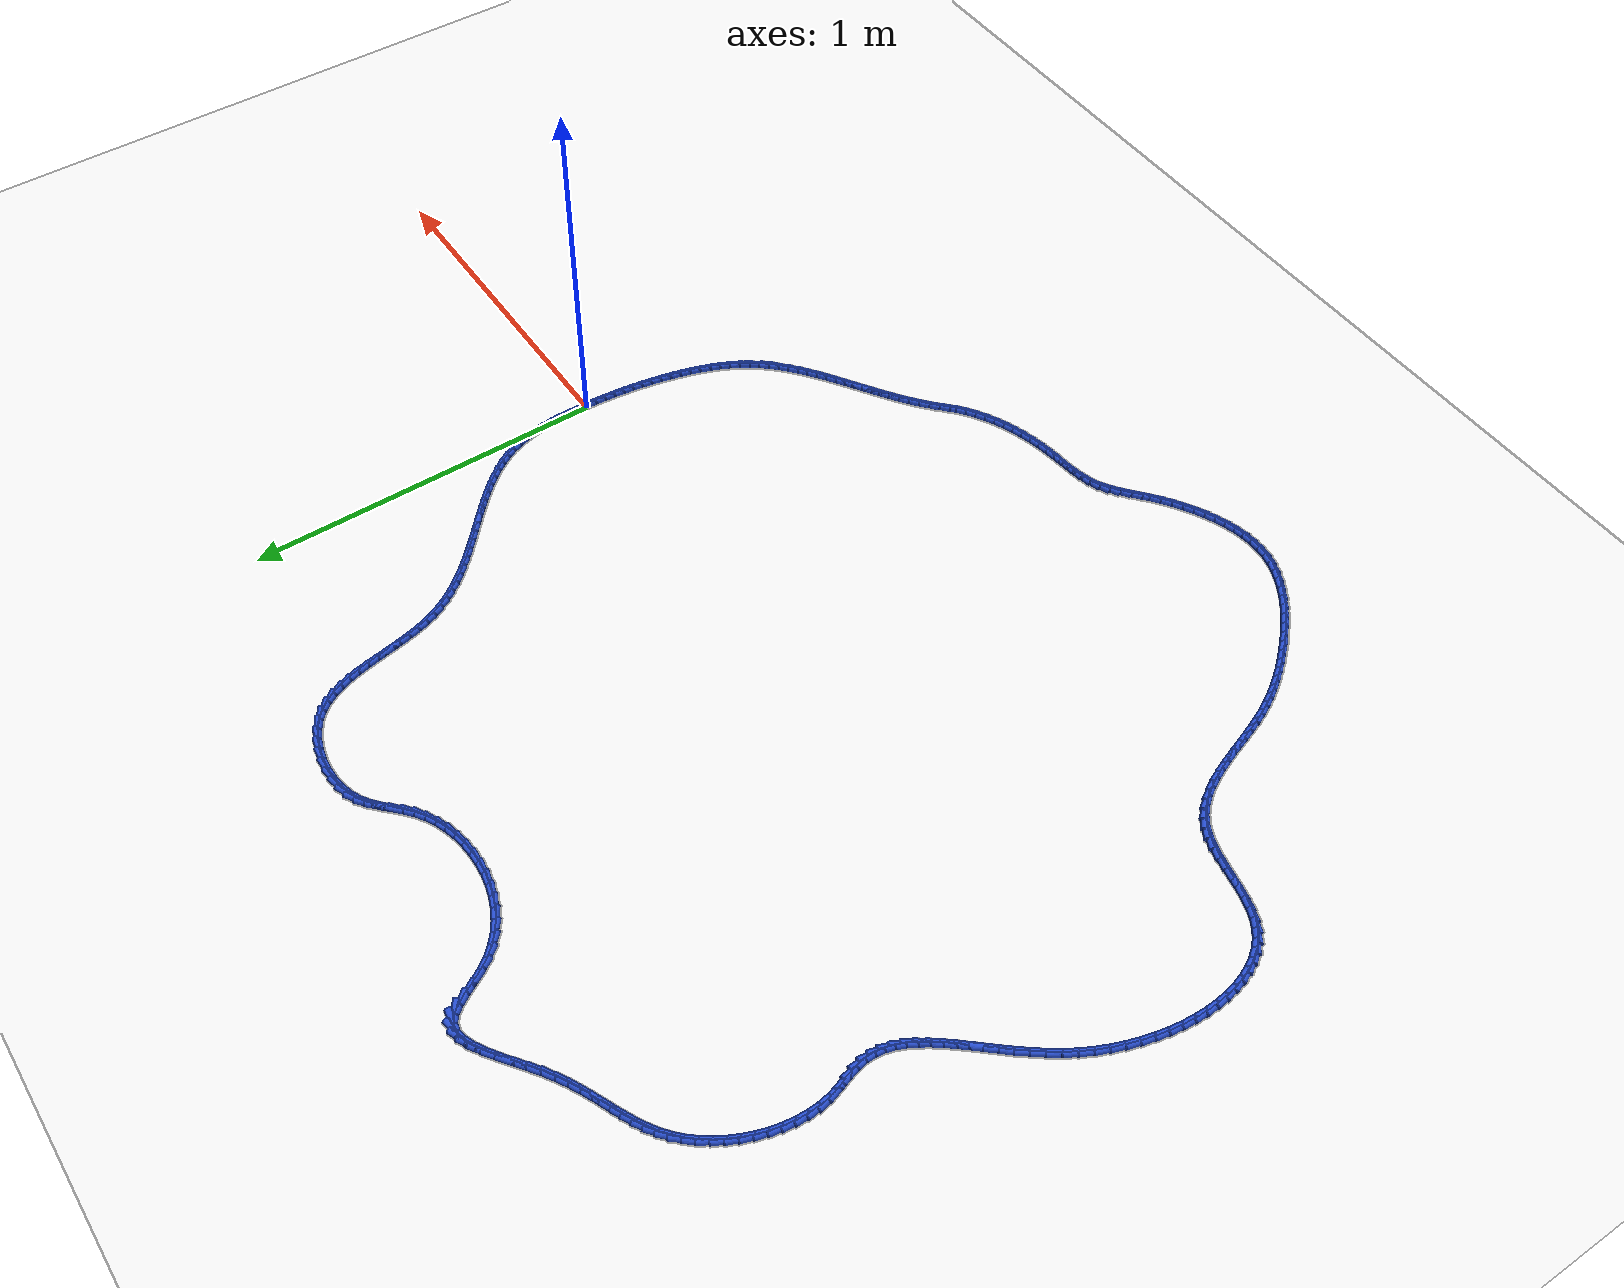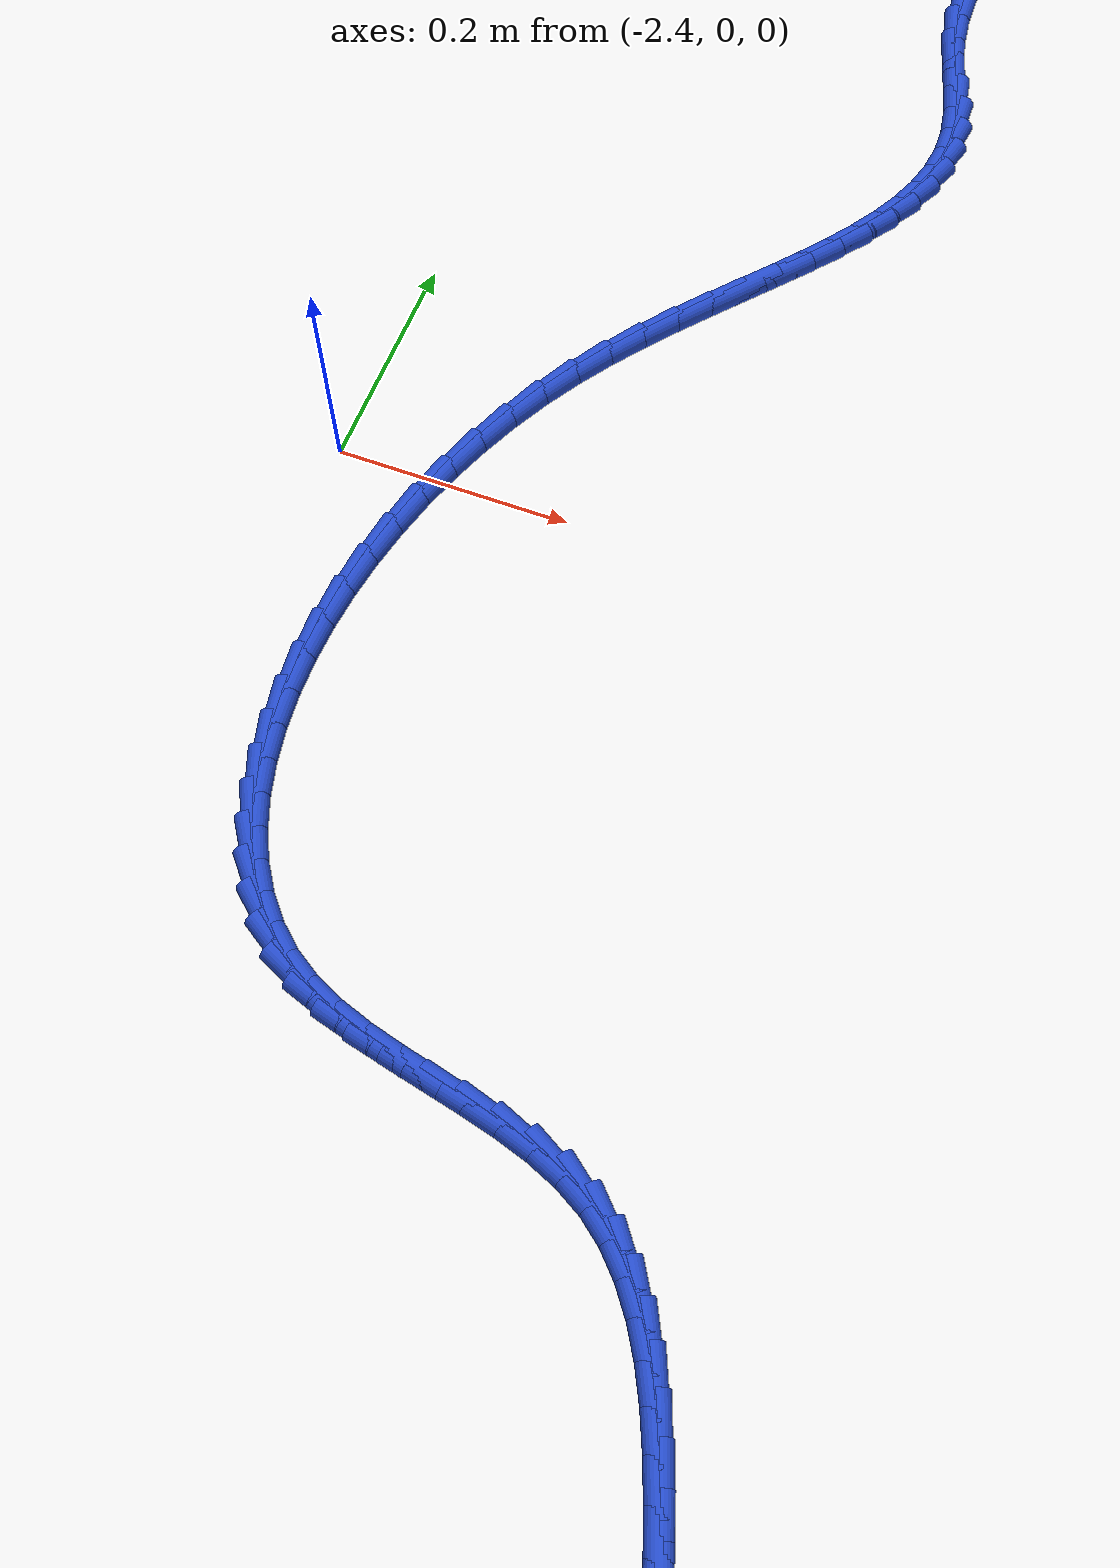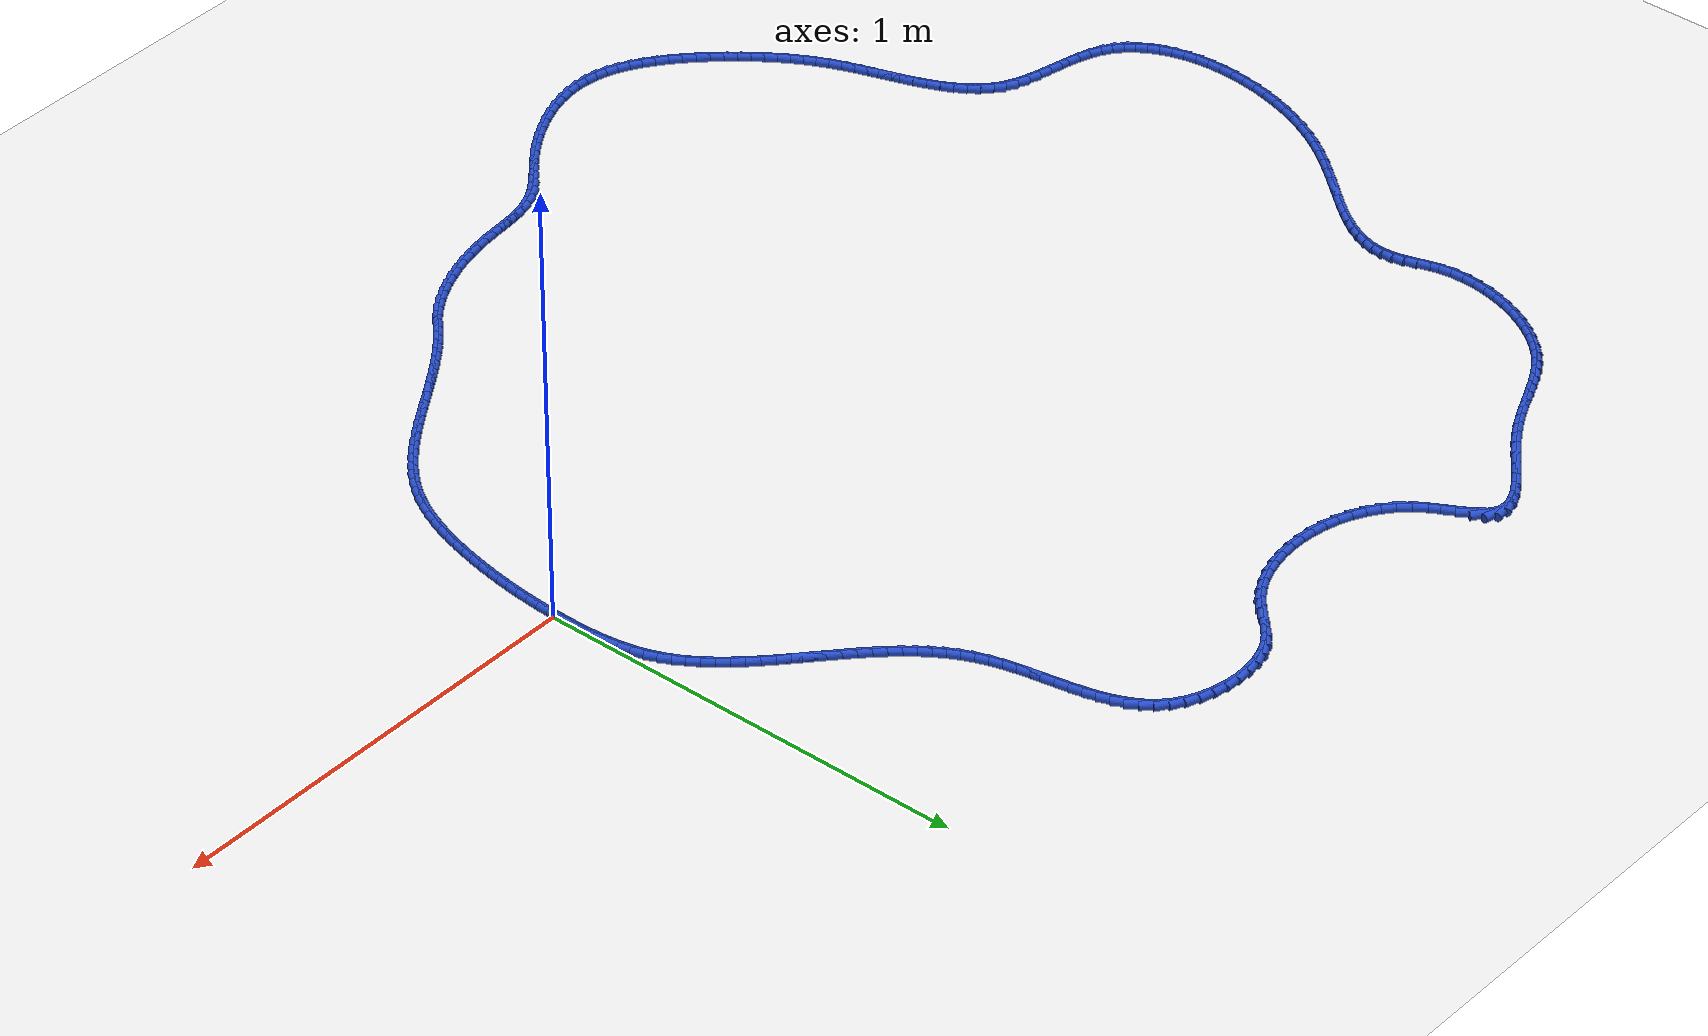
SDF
<sdf version="1.6">
 <world name="default">
  <light name="sun" type="directional">
   <pose>0 0 10 0 -0 0</pose>
   <diffuse>0.8 0.8 0.8 1</diffuse>
   <specular>0.2 0.2 0.2 1</specular>
   <attenuation>
    <range>1000</range>
    <constant>0.9</constant>
    <linear>0.01</linear>
    <quadratic>0.001</quadratic>
   </attenuation>
   <direction>-0.5 0.1 -0.9</direction>
  </light>
  <model name="ground_plane">
   <static>1</static>
   <link name="link">
    <collision name="collision">
     <geometry><plane><normal>0 0 1</normal><size>100 100</size></plane></geometry>
     <surface><friction><ode><mu>100</mu><mu2>50</mu2></ode></friction></surface>
    </collision>
    <visual name="visual">
     <cast_shadows>0</cast_shadows>
     <geometry><plane><normal>0 0 1</normal><size>100 100</size></plane></geometry>
     <material>
      <script><uri>file://media/materials/scripts/gazebo.material</uri><name>Gazebo/WhiteGlow</name></script>
     </material>
    </visual>
   </link>
  </model>
  <gravity>0 0 -9.8</gravity>
  <magnetic_field>6e-06 2.3e-05 -4.2e-05</magnetic_field>
  <atmosphere type="adiabatic"/>
  <physics name="default_physics" default="0" type="ode">
   <max_step_size>0.001</max_step_size>
   <real_time_factor>1</real_time_factor>
   <real_time_update_rate>1000</real_time_update_rate>
  </physics>
  <scene><ambient>0.4 0.4 0.4 1</ambient><background>0.7 0.7 0.7 1</background><shadows>1</shadows></scene>
  <spherical_coordinates>
   <surface_model>EARTH_WGS84</surface_model>
   <latitude_deg>0</latitude_deg>
   <longitude_deg>0</longitude_deg>
   <elevation>0</elevation>
   <heading_deg>0</heading_deg>
  </spherical_coordinates>
  <model name="line">
   <link name="link_0">
    <pose>5.5294310796760726e-18 0.0 0.01 0 1.57 1.5444436091295004</pose>
    <collision name="collision">
     <geometry><cylinder><radius>0.01</radius><length>0.08</length></cylinder></geometry>
    </collision>
    <visual name="visual">
     <material>
      <script><name>Gazebo/Blue</name><uri>file://media/materials/scripts/gazebo.material</uri></script>
     </material>
     <geometry><cylinder><radius>0.01</radius><length>0.08</length></cylinder></geometry>
    </visual>
   </link>
   <link name="link_1">
    <pose>0.0007724250891138013 0.029304236589794443 0.01 0 1.57 1.5688253961860097</pose>
    <collision name="collision">
     <geometry><cylinder><radius>0.01</radius><length>0.08</length></cylinder></geometry>
    </collision>
    <visual name="visual">
     <material>
      <script><name>Gazebo/Blue</name><uri>file://media/materials/scripts/gazebo.material</uri></script>
     </material>
     <geometry><cylinder><radius>0.01</radius><length>0.08</length></cylinder></geometry>
    </visual>
   </link>
   <link name="link_2">
    <pose>0.0008304526359340504 0.05874589801677482 0.01 0 1.57 -1.541692237862683</pose>
    <collision name="collision">
     <geometry><cylinder><radius>0.01</radius><length>0.08</length></cylinder></geometry>
    </collision>
    <visual name="visual">
     <material>
      <script><name>Gazebo/Blue</name><uri>file://media/materials/scripts/gazebo.material</uri></script>
     </material>
     <geometry><cylinder><radius>0.01</radius><length>0.08</length></cylinder></geometry>
    </visual>
   </link>
   <link name="link_3">
    <pose>-2.5676761053213806e-05 0.08815371276634205 0.01 0 1.57 -1.5034372966438714</pose>
    <collision name="collision">
     <geometry><cylinder><radius>0.01</radius><length>0.08</length></cylinder></geometry>
    </collision>
    <visual name="visual">
     <material>
      <script><name>Gazebo/Blue</name><uri>file://media/materials/scripts/gazebo.material</uri></script>
     </material>
     <geometry><cylinder><radius>0.01</radius><length>0.08</length></cylinder></geometry>
    </visual>
   </link>
   <link name="link_4">
    <pose>-0.0019957225033619525 0.1173564093238969 0.01 0 1.57 -1.457371203074615</pose>
    <collision name="collision">
     <geometry><cylinder><radius>0.01</radius><length>0.08</length></cylinder></geometry>
    </collision>
    <visual name="visual">
     <material>
      <script><name>Gazebo/Blue</name><uri>file://media/materials/scripts/gazebo.material</uri></script>
     </material>
     <geometry><cylinder><radius>0.01</radius><length>0.08</length></cylinder></geometry>
    </visual>
   </link>
   <link name="link_5">
    <pose>-0.005279443992506131 0.14618271617484047 0.01 0 1.57 -1.4027572063622549</pose>
    <collision name="collision">
     <geometry><cylinder><radius>0.01</radius><length>0.08</length></cylinder></geometry>
    </collision>
    <visual name="visual">
     <material>
      <script><name>Gazebo/Blue</name><uri>file://media/materials/scripts/gazebo.material</uri></script>
     </material>
     <geometry><cylinder><radius>0.01</radius><length>0.08</length></cylinder></geometry>
    </visual>
   </link>
   <link name="link_6">
    <pose>-0.01007660062999971 0.1744613618045734 0.01 0 1.57 -1.3388218000715582</pose>
    <collision name="collision">
     <geometry><cylinder><radius>0.01</radius><length>0.08</length></cylinder></geometry>
    </collision>
    <visual name="visual">
     <material>
      <script><name>Gazebo/Blue</name><uri>file://media/materials/scripts/gazebo.material</uri></script>
     </material>
     <geometry><cylinder><radius>0.01</radius><length>0.08</length></cylinder></geometry>
    </visual>
   </link>
   <link name="link_7">
    <pose>-0.016586951817356657 0.2020210746984967 0.01 0 1.57 -1.2648712547799625</pose>
    <collision name="collision">
     <geometry><cylinder><radius>0.01</radius><length>0.08</length></cylinder></geometry>
    </collision>
    <visual name="visual">
     <material>
      <script><name>Gazebo/Blue</name><uri>file://media/materials/scripts/gazebo.material</uri></script>
     </material>
     <geometry><cylinder><radius>0.01</radius><length>0.08</length></cylinder></geometry>
    </visual>
   </link>
   <link name="link_8">
    <pose>-0.025010256956090927 0.22869058334201112 0.01 0 1.57 -1.1810644103449333</pose>
    <collision name="collision">
     <geometry><cylinder><radius>0.01</radius><length>0.08</length></cylinder></geometry>
    </collision>
    <visual name="visual">
     <material>
      <script><name>Gazebo/Blue</name><uri>file://media/materials/scripts/gazebo.material</uri></script>
     </material>
     <geometry><cylinder><radius>0.01</radius><length>0.08</length></cylinder></geometry>
    </visual>
   </link>
   <link name="link_9">
    <pose>-0.03553248622592734 0.2543082224170626 0.01 0 1.57 -1.0969023636849762</pose>
    <collision name="collision">
     <geometry><cylinder><radius>0.01</radius><length>0.08</length></cylinder></geometry>
    </collision>
    <visual name="visual">
     <material>
      <script><name>Gazebo/Blue</name><uri>file://media/materials/scripts/gazebo.material</uri></script>
     </material>
     <geometry><cylinder><radius>0.01</radius><length>0.08</length></cylinder></geometry>
    </visual>
   </link>
   <link name="link_10">
    <pose>-0.04812529734116499 0.27886162637728334 0.01 0 1.57 -1.0207997346557616</pose>
    <collision name="collision">
     <geometry><cylinder><radius>0.01</radius><length>0.08</length></cylinder></geometry>
    </collision>
    <visual name="visual">
     <material>
      <script><name>Gazebo/Blue</name><uri>file://media/materials/scripts/gazebo.material</uri></script>
     </material>
     <geometry><cylinder><radius>0.01</radius><length>0.08</length></cylinder></geometry>
    </visual>
   </link>
   <link name="link_11">
    <pose>-0.06259118820945592 0.30245627406049 0.01 0 1.57 -0.9537348469507666</pose>
    <collision name="collision">
     <geometry><cylinder><radius>0.01</radius><length>0.08</length></cylinder></geometry>
    </collision>
    <visual name="visual">
     <material>
      <script><name>Gazebo/Blue</name><uri>file://media/materials/scripts/gazebo.material</uri></script>
     </material>
     <geometry><cylinder><radius>0.01</radius><length>0.08</length></cylinder></geometry>
    </visual>
   </link>
   <link name="link_12">
    <pose>-0.07872805680326588 0.3252008488277252 0.01 0 1.57 -0.8959668193594053</pose>
    <collision name="collision">
     <geometry><cylinder><radius>0.01</radius><length>0.08</length></cylinder></geometry>
    </collision>
    <visual name="visual">
     <material>
      <script><name>Gazebo/Blue</name><uri>file://media/materials/scripts/gazebo.material</uri></script>
     </material>
     <geometry><cylinder><radius>0.01</radius><length>0.08</length></cylinder></geometry>
    </visual>
   </link>
   <link name="link_13">
    <pose>-0.09633380109506066 0.34720403404003164 0.01 0 1.57 -0.8473905716731159</pose>
    <collision name="collision">
     <geometry><cylinder><radius>0.01</radius><length>0.08</length></cylinder></geometry>
    </collision>
    <visual name="visual">
     <material>
      <script><name>Gazebo/Blue</name><uri>file://media/materials/scripts/gazebo.material</uri></script>
     </material>
     <geometry><cylinder><radius>0.01</radius><length>0.08</length></cylinder></geometry>
    </visual>
   </link>
   <link name="link_14">
    <pose>-0.11520631905730598 0.3685745130584516 0.01 0 1.57 -0.8076893527655452</pose>
    <collision name="collision">
     <geometry><cylinder><radius>0.01</radius><length>0.08</length></cylinder></geometry>
    </collision>
    <visual name="visual">
     <material>
      <script><name>Gazebo/Blue</name><uri>file://media/materials/scripts/gazebo.material</uri></script>
     </material>
     <geometry><cylinder><radius>0.01</radius><length>0.08</length></cylinder></geometry>
    </visual>
   </link>
   <link name="link_15">
    <pose>-0.13514350866246758 0.3894209692440279 0.01 0 1.57 -0.7764574684508303</pose>
    <collision name="collision">
     <geometry><cylinder><radius>0.01</radius><length>0.08</length></cylinder></geometry>
    </collision>
    <visual name="visual">
     <material>
      <script><name>Gazebo/Blue</name><uri>file://media/materials/scripts/gazebo.material</uri></script>
     </material>
     <geometry><cylinder><radius>0.01</radius><length>0.08</length></cylinder></geometry>
    </visual>
   </link>
   <link name="link_16">
    <pose>-0.15594326788301122 0.4098520859578029 0.01 0 1.57 -0.7532876159876892</pose>
    <collision name="collision">
     <geometry><cylinder><radius>0.01</radius><length>0.08</length></cylinder></geometry>
    </collision>
    <visual name="visual">
     <material>
      <script><name>Gazebo/Blue</name><uri>file://media/materials/scripts/gazebo.material</uri></script>
     </material>
     <geometry><cylinder><radius>0.01</radius><length>0.08</length></cylinder></geometry>
    </visual>
   </link>
   <link name="link_17">
    <pose>-0.17740349469140276 0.4299765465608194 0.01 0 1.57 -0.7378274195153731</pose>
    <collision name="collision">
     <geometry><cylinder><radius>0.01</radius><length>0.08</length></cylinder></geometry>
    </collision>
    <visual name="visual">
     <material>
      <script><name>Gazebo/Blue</name><uri>file://media/materials/scripts/gazebo.material</uri></script>
     </material>
     <geometry><cylinder><radius>0.01</radius><length>0.08</length></cylinder></geometry>
    </visual>
   </link>
   <link name="link_18">
    <pose>-0.19932208706010776 0.4499030344141197 0.01 0 1.57 -0.729812941264067</pose>
    <collision name="collision">
     <geometry><cylinder><radius>0.01</radius><length>0.08</length></cylinder></geometry>
    </collision>
    <visual name="visual">
     <material>
      <script><name>Gazebo/Blue</name><uri>file://media/materials/scripts/gazebo.material</uri></script>
     </material>
     <geometry><cylinder><radius>0.01</radius><length>0.08</length></cylinder></geometry>
    </visual>
   </link>
   <link name="link_19">
    <pose>-0.22149694296159214 0.46974023287874656 0.01 0 1.57 -0.7290863556445583</pose>
    <collision name="collision">
     <geometry><cylinder><radius>0.01</radius><length>0.08</length></cylinder></geometry>
    </collision>
    <visual name="visual">
     <material>
      <script><name>Gazebo/Blue</name><uri>file://media/materials/scripts/gazebo.material</uri></script>
     </material>
     <geometry><cylinder><radius>0.01</radius><length>0.08</length></cylinder></geometry>
    </visual>
   </link>
   <link name="link_20">
    <pose>-0.2437259603683215 0.4895968253157424 0.01 0 1.57 -0.7356029198248915</pose>
    <collision name="collision">
     <geometry><cylinder><radius>0.01</radius><length>0.08</length></cylinder></geometry>
    </collision>
    <visual name="visual">
     <material>
      <script><name>Gazebo/Blue</name><uri>file://media/materials/scripts/gazebo.material</uri></script>
     </material>
     <geometry><cylinder><radius>0.01</radius><length>0.08</length></cylinder></geometry>
    </visual>
   </link>
   <link name="link_21">
    <pose>-0.2658070372527618 0.5095814950861499 0.01 0 1.57 -0.7494300069341955</pose>
    <collision name="collision">
     <geometry><cylinder><radius>0.01</radius><length>0.08</length></cylinder></geometry>
    </collision>
    <visual name="visual">
     <material>
      <script><name>Gazebo/Blue</name><uri>file://media/materials/scripts/gazebo.material</uri></script>
     </material>
     <geometry><cylinder><radius>0.01</radius><length>0.08</length></cylinder></geometry>
    </visual>
   </link>
   <link name="link_22">
    <pose>-0.28753807158737854 0.5298029255510115 0.01 0 1.57 -0.7707386786312679</pose>
    <collision name="collision">
     <geometry><cylinder><radius>0.01</radius><length>0.08</length></cylinder></geometry>
    </collision>
    <visual name="visual">
     <material>
      <script><name>Gazebo/Blue</name><uri>file://media/materials/scripts/gazebo.material</uri></script>
     </material>
     <geometry><cylinder><radius>0.01</radius><length>0.08</length></cylinder></geometry>
    </visual>
   </link>
   <link name="link_23">
    <pose>-0.3087169613446378 0.5503698000713702 0.01 0 1.57 -0.7997861076880881</pose>
    <collision name="collision">
     <geometry><cylinder><radius>0.01</radius><length>0.08</length></cylinder></geometry>
    </collision>
    <visual name="visual">
     <material>
      <script><name>Gazebo/Blue</name><uri>file://media/materials/scripts/gazebo.material</uri></script>
     </material>
     <geometry><cylinder><radius>0.01</radius><length>0.08</length></cylinder></geometry>
    </visual>
   </link>
   <link name="link_24">
    <pose>-0.32914160449700497 0.5713908020082679 0.01 0 1.57 -0.8368851310237811</pose>
    <collision name="collision">
     <geometry><cylinder><radius>0.01</radius><length>0.08</length></cylinder></geometry>
    </collision>
    <visual name="visual">
     <material>
      <script><name>Gazebo/Blue</name><uri>file://media/materials/scripts/gazebo.material</uri></script>
     </material>
     <geometry><cylinder><radius>0.01</radius><length>0.08</length></cylinder></geometry>
    </visual>
   </link>
   <link name="link_25">
    <pose>-0.34860989901694606 0.5929746147227476 0.01 0 1.57 -0.8823555700988243</pose>
    <collision name="collision">
     <geometry><cylinder><radius>0.01</radius><length>0.08</length></cylinder></geometry>
    </collision>
    <visual name="visual">
     <material>
      <script><name>Gazebo/Blue</name><uri>file://media/materials/scripts/gazebo.material</uri></script>
     </material>
     <geometry><cylinder><radius>0.01</radius><length>0.08</length></cylinder></geometry>
    </visual>
   </link>
   <link name="link_26">
    <pose>-0.36691974287692675 0.6152299215758517 0.01 0 1.57 -0.9364514772531675</pose>
    <collision name="collision">
     <geometry><cylinder><radius>0.01</radius><length>0.08</length></cylinder></geometry>
    </collision>
    <visual name="visual">
     <material>
      <script><name>Gazebo/Blue</name><uri>file://media/materials/scripts/gazebo.material</uri></script>
     </material>
     <geometry><cylinder><radius>0.01</radius><length>0.08</length></cylinder></geometry>
    </visual>
   </link>
   <link name="link_27">
    <pose>-0.3838690340494128 0.638265405928623 0.01 0 1.57 -0.9992607071051856</pose>
    <collision name="collision">
     <geometry><cylinder><radius>0.01</radius><length>0.08</length></cylinder></geometry>
    </collision>
    <visual name="visual">
     <material>
      <script><name>Gazebo/Blue</name><uri>file://media/materials/scripts/gazebo.material</uri></script>
     </material>
     <geometry><cylinder><radius>0.01</radius><length>0.08</length></cylinder></geometry>
    </visual>
   </link>
   <link name="link_28">
    <pose>-0.3992556705068699 0.6621897511421038 0.01 0 1.57 -1.0704266466682988</pose>
    <collision name="collision">
     <geometry><cylinder><radius>0.01</radius><length>0.08</length></cylinder></geometry>
    </collision>
    <visual name="visual">
     <material>
      <script><name>Gazebo/Blue</name><uri>file://media/materials/scripts/gazebo.material</uri></script>
     </material>
     <geometry><cylinder><radius>0.01</radius><length>0.08</length></cylinder></geometry>
    </visual>
   </link>
   <link name="link_29">
    <pose>-0.4128821858875326 0.6871110186877395 0.01 0 1.57 -1.1453547257778394</pose>
    <collision name="collision">
     <geometry><cylinder><radius>0.01</radius><length>0.08</length></cylinder></geometry>
    </collision>
    <visual name="visual">
     <material>
      <script><name>Gazebo/Blue</name><uri>file://media/materials/scripts/gazebo.material</uri></script>
     </material>
     <geometry><cylinder><radius>0.01</radius><length>0.08</length></cylinder></geometry>
    </visual>
   </link>
   <link name="link_30">
    <pose>-0.42466797528614864 0.7131215926935821 0.01 0 1.57 -1.2186103788120048</pose>
    <collision name="collision">
     <geometry><cylinder><radius>0.01</radius><length>0.08</length></cylinder></geometry>
    </collision>
    <visual name="visual">
     <material>
      <script><name>Gazebo/Blue</name><uri>file://media/materials/scripts/gazebo.material</uri></script>
     </material>
     <geometry><cylinder><radius>0.01</radius><length>0.08</length></cylinder></geometry>
    </visual>
   </link>
   <link name="link_31">
    <pose>-0.4346552848783043 0.7402973764167603 0.01 0 1.57 -1.2864585584660118</pose>
    <collision name="collision">
     <geometry><cylinder><radius>0.01</radius><length>0.08</length></cylinder></geometry>
    </collision>
    <visual name="visual">
     <material>
      <script><name>Gazebo/Blue</name><uri>file://media/materials/scripts/gazebo.material</uri></script>
     </material>
     <geometry><cylinder><radius>0.01</radius><length>0.08</length></cylinder></geometry>
    </visual>
   </link>
   <link name="link_32">
    <pose>-0.44294422884036827 0.7686592407112293 0.01 0 1.57 -1.3381907718266544</pose>
    <collision name="collision">
     <geometry><cylinder><radius>0.01</radius><length>0.08</length></cylinder></geometry>
    </collision>
    <visual name="visual">
     <material>
      <script><name>Gazebo/Blue</name><uri>file://media/materials/scripts/gazebo.material</uri></script>
     </material>
     <geometry><cylinder><radius>0.01</radius><length>0.08</length></cylinder></geometry>
    </visual>
   </link>
   <link name="link_33">
    <pose>-0.44988670191475766 0.7979655520236304 0.01 0 1.57 -1.3721808116540402</pose>
    <collision name="collision">
     <geometry><cylinder><radius>0.01</radius><length>0.08</length></cylinder></geometry>
    </collision>
    <visual name="visual">
     <material>
      <script><name>Gazebo/Blue</name><uri>file://media/materials/scripts/gazebo.material</uri></script>
     </material>
     <geometry><cylinder><radius>0.01</radius><length>0.08</length></cylinder></geometry>
    </visual>
   </link>
   <link name="link_34">
    <pose>-0.4559106513829668 0.8278953850307587 0.01 0 1.57 -1.3897716146046102</pose>
    <collision name="collision">
     <geometry><cylinder><radius>0.01</radius><length>0.08</length></cylinder></geometry>
    </collision>
    <visual name="visual">
     <material>
      <script><name>Gazebo/Blue</name><uri>file://media/materials/scripts/gazebo.material</uri></script>
     </material>
     <geometry><cylinder><radius>0.01</radius><length>0.08</length></cylinder></geometry>
    </visual>
   </link>
   <link name="link_35">
    <pose>-0.46144404059443195 0.8581277976570998 0.01 0 1.57 -1.3916692696389064</pose>
    <collision name="collision">
     <geometry><cylinder><radius>0.01</radius><length>0.08</length></cylinder></geometry>
    </collision>
    <visual name="visual">
     <material>
      <script><name>Gazebo/Blue</name><uri>file://media/materials/scripts/gazebo.material</uri></script>
     </material>
     <geometry><cylinder><radius>0.01</radius><length>0.08</length></cylinder></geometry>
    </visual>
   </link>
   <link name="link_36">
    <pose>-0.4669148328985895 0.8883418478271403 0.01 0 1.57 -1.3778717919321029</pose>
    <collision name="collision">
     <geometry><cylinder><radius>0.01</radius><length>0.08</length></cylinder></geometry>
    </collision>
    <visual name="visual">
     <material>
      <script><name>Gazebo/Blue</name><uri>file://media/materials/scripts/gazebo.material</uri></script>
     </material>
     <geometry><cylinder><radius>0.01</radius><length>0.08</length></cylinder></geometry>
    </visual>
   </link>
   <link name="link_37">
    <pose>-0.47275099164487583 0.9182165934653661 0.01 0 1.57 -1.3476507782210265</pose>
    <collision name="collision">
     <geometry><cylinder><radius>0.01</radius><length>0.08</length></cylinder></geometry>
    </collision>
    <visual name="visual">
     <material>
      <script><name>Gazebo/Blue</name><uri>file://media/materials/scripts/gazebo.material</uri></script>
     </material>
     <geometry><cylinder><radius>0.01</radius><length>0.08</length></cylinder></geometry>
    </visual>
   </link>
   <link name="link_38">
    <pose>-0.47938048018272733 0.9474310924962641 0.01 0 1.57 -1.2995800134300388</pose>
    <collision name="collision">
     <geometry><cylinder><radius>0.01</radius><length>0.08</length></cylinder></geometry>
    </collision>
    <visual name="visual">
     <material>
      <script><name>Gazebo/Blue</name><uri>file://media/materials/scripts/gazebo.material</uri></script>
     </material>
     <geometry><cylinder><radius>0.01</radius><length>0.08</length></cylinder></geometry>
    </visual>
   </link>
   <link name="link_39">
    <pose>-0.48723126186158044 0.9756644028443203 0.01 0 1.57 -1.2316715903046354</pose>
    <collision name="collision">
     <geometry><cylinder><radius>0.01</radius><length>0.08</length></cylinder></geometry>
    </collision>
    <visual name="visual">
     <material>
      <script><name>Gazebo/Blue</name><uri>file://media/materials/scripts/gazebo.material</uri></script>
     </material>
     <geometry><cylinder><radius>0.01</radius><length>0.08</length></cylinder></geometry>
    </visual>
   </link>
   <link name="link_40">
    <pose>-0.49673130003087146 1.0025955824340207 0.01 0 1.57 -1.141762167571544</pose>
    <collision name="collision">
     <geometry><cylinder><radius>0.01</radius><length>0.08</length></cylinder></geometry>
    </collision>
    <visual name="visual">
     <material>
      <script><name>Gazebo/Blue</name><uri>file://media/materials/scripts/gazebo.material</uri></script>
     </material>
     <geometry><cylinder><radius>0.01</radius><length>0.08</length></cylinder></geometry>
    </visual>
   </link>
   <link name="link_41">
    <pose>-0.5083085580400366 1.0279036891898519 0.01 0 1.57 -1.0283655454468543</pose>
    <collision name="collision">
     <geometry><cylinder><radius>0.01</radius><length>0.08</length></cylinder></geometry>
    </collision>
    <visual name="visual">
     <material>
      <script><name>Gazebo/Blue</name><uri>file://media/materials/scripts/gazebo.material</uri></script>
     </material>
     <geometry><cylinder><radius>0.01</radius><length>0.08</length></cylinder></geometry>
    </visual>
   </link>
   <link name="link_42">
    <pose>-0.5223909992385125 1.0512677810363003 0.01 0 1.57 -0.8921293446321586</pose>
    <collision name="collision">
     <geometry><cylinder><radius>0.01</radius><length>0.08</length></cylinder></geometry>
    </collision>
    <visual name="visual">
     <material>
      <script><name>Gazebo/Blue</name><uri>file://media/materials/scripts/gazebo.material</uri></script>
     </material>
     <geometry><cylinder><radius>0.01</radius><length>0.08</length></cylinder></geometry>
    </visual>
   </link>
   <link name="link_43">
    <pose>-0.5394065869757356 1.072366915897852 0.01 0 1.57 -0.7375227879521923</pose>
    <collision name="collision">
     <geometry><cylinder><radius>0.01</radius><length>0.08</length></cylinder></geometry>
    </collision>
    <visual name="visual">
     <material>
      <script><name>Gazebo/Blue</name><uri>file://media/materials/scripts/gazebo.material</uri></script>
     </material>
     <geometry><cylinder><radius>0.01</radius><length>0.08</length></cylinder></geometry>
    </visual>
   </link>
   <link name="link_44">
    <pose>-0.5597831358702835 1.0908801767481944 0.01 0 1.57 -0.5795076866644713</pose>
    <collision name="collision">
     <geometry><cylinder><radius>0.01</radius><length>0.08</length></cylinder></geometry>
    </collision>
    <visual name="visual">
     <material>
      <script><name>Gazebo/Blue</name><uri>file://media/materials/scripts/gazebo.material</uri></script>
     </material>
     <geometry><cylinder><radius>0.01</radius><length>0.08</length></cylinder></geometry>
    </visual>
   </link>
   <link name="link_45">
    <pose>-0.5836946092590553 1.1065294001090693 0.01 0 1.57 -0.4399565210279161</pose>
    <collision name="collision">
     <geometry><cylinder><radius>0.01</radius><length>0.08</length></cylinder></geometry>
    </collision>
    <visual name="visual">
     <material>
      <script><name>Gazebo/Blue</name><uri>file://media/materials/scripts/gazebo.material</uri></script>
     </material>
     <geometry><cylinder><radius>0.01</radius><length>0.08</length></cylinder></geometry>
    </visual>
   </link>
   <link name="link_46">
    <pose>-0.6105410659970562 1.1191667632365165 0.01 0 1.57 -0.3162928248825869</pose>
    <collision name="collision">
     <geometry><cylinder><radius>0.01</radius><length>0.08</length></cylinder></geometry>
    </collision>
    <visual name="visual">
     <material>
      <script><name>Gazebo/Blue</name><uri>file://media/materials/scripts/gazebo.material</uri></script>
     </material>
     <geometry><cylinder><radius>0.01</radius><length>0.08</length></cylinder></geometry>
    </visual>
   </link>
   <link name="link_47">
    <pose>-0.6395756111712234 1.128669193291096 0.01 0 1.57 -0.20210090492745897</pose>
    <collision name="collision">
     <geometry><cylinder><radius>0.01</radius><length>0.08</length></cylinder></geometry>
    </collision>
    <visual name="visual">
     <material>
      <script><name>Gazebo/Blue</name><uri>file://media/materials/scripts/gazebo.material</uri></script>
     </material>
     <geometry><cylinder><radius>0.01</radius><length>0.08</length></cylinder></geometry>
    </visual>
   </link>
   <link name="link_48">
    <pose>-0.6700513498684959 1.1349136174333703 0.01 0 1.57 -0.09160501299704839</pose>
    <collision name="collision">
     <geometry><cylinder><radius>0.01</radius><length>0.08</length></cylinder></geometry>
    </collision>
    <visual name="visual">
     <material>
      <script><name>Gazebo/Blue</name><uri>file://media/materials/scripts/gazebo.material</uri></script>
     </material>
     <geometry><cylinder><radius>0.01</radius><length>0.08</length></cylinder></geometry>
    </visual>
   </link>
   <link name="link_49">
    <pose>-0.7012213871758115 1.1377769628239014 0.01 0 1.57 0.020590241970216902</pose>
    <collision name="collision">
     <geometry><cylinder><radius>0.01</radius><length>0.08</length></cylinder></geometry>
    </collision>
    <visual name="visual">
     <material>
      <script><name>Gazebo/Blue</name><uri>file://media/materials/scripts/gazebo.material</uri></script>
     </material>
     <geometry><cylinder><radius>0.01</radius><length>0.08</length></cylinder></geometry>
    </visual>
   </link>
   <link name="link_50">
    <pose>-0.7323388281801083 1.1371361566232505 0.01 0 1.57 0.1398566497385695</pose>
    <collision name="collision">
     <geometry><cylinder><radius>0.01</radius><length>0.08</length></cylinder></geometry>
    </collision>
    <visual name="visual">
     <material>
      <script><name>Gazebo/Blue</name><uri>file://media/materials/scripts/gazebo.material</uri></script>
     </material>
     <geometry><cylinder><radius>0.01</radius><length>0.08</length></cylinder></geometry>
    </visual>
   </link>
   <link name="link_51">
    <pose>-0.7626567779683251 1.1328681259919802 0.01 0 1.57 0.271792909332439</pose>
    <collision name="collision">
     <geometry><cylinder><radius>0.01</radius><length>0.08</length></cylinder></geometry>
    </collision>
    <visual name="visual">
     <material>
      <script><name>Gazebo/Blue</name><uri>file://media/materials/scripts/gazebo.material</uri></script>
     </material>
     <geometry><cylinder><radius>0.01</radius><length>0.08</length></cylinder></geometry>
    </visual>
   </link>
   <link name="link_52">
    <pose>-0.7914283416273996 1.124849798090652 0.01 0 1.57 0.42211470220724173</pose>
    <collision name="collision">
     <geometry><cylinder><radius>0.01</radius><length>0.08</length></cylinder></geometry>
    </collision>
    <visual name="visual">
     <material>
      <script><name>Gazebo/Blue</name><uri>file://media/materials/scripts/gazebo.material</uri></script>
     </material>
     <geometry><cylinder><radius>0.01</radius><length>0.08</length></cylinder></geometry>
    </visual>
   </link>
   <link name="link_53">
    <pose>-0.8179066242442696 1.1129581000798272 0.01 0 1.57 0.5865241983206736</pose>
    <collision name="collision">
     <geometry><cylinder><radius>0.01</radius><length>0.08</length></cylinder></geometry>
    </collision>
    <visual name="visual">
     <material>
      <script><name>Gazebo/Blue</name><uri>file://media/materials/scripts/gazebo.material</uri></script>
     </material>
     <geometry><cylinder><radius>0.01</radius><length>0.08</length></cylinder></geometry>
    </visual>
   </link>
   <link name="link_54">
    <pose>-0.8415620852240826 1.0972382586843332 0.01 0 1.57 0.7109046088940874</pose>
    <collision name="collision">
     <geometry><cylinder><radius>0.01</radius><length>0.08</length></cylinder></geometry>
    </collision>
    <visual name="visual">
     <material>
      <script><name>Gazebo/Blue</name><uri>file://media/materials/scripts/gazebo.material</uri></script>
     </material>
     <geometry><cylinder><radius>0.01</radius><length>0.08</length></cylinder></geometry>
    </visual>
   </link>
   <link name="link_55">
    <pose>-0.8631001644615963 1.078691758043114 0.01 0 1.57 0.7724084802625105</pose>
    <collision name="collision">
     <geometry><cylinder><radius>0.01</radius><length>0.08</length></cylinder></geometry>
    </collision>
    <visual name="visual">
     <material>
      <script><name>Gazebo/Blue</name><uri>file://media/materials/scripts/gazebo.material</uri></script>
     </material>
     <geometry><cylinder><radius>0.01</radius><length>0.08</length></cylinder></geometry>
    </visual>
   </link>
   <link name="link_56">
    <pose>-0.8836619072056336 1.0586573757608468 0.01 0 1.57 0.7721054160212065</pose>
    <collision name="collision">
     <geometry><cylinder><radius>0.01</radius><length>0.08</length></cylinder></geometry>
    </collision>
    <visual name="visual">
     <material>
      <script><name>Gazebo/Blue</name><uri>file://media/materials/scripts/gazebo.material</uri></script>
     </material>
     <geometry><cylinder><radius>0.01</radius><length>0.08</length></cylinder></geometry>
    </visual>
   </link>
   <link name="link_57">
    <pose>-0.9043888511766754 1.0384742707678076 0.01 0 1.57 0.7114100335788597</pose>
    <collision name="collision">
     <geometry><cylinder><radius>0.01</radius><length>0.08</length></cylinder></geometry>
    </collision>
    <visual name="visual">
     <material>
      <script><name>Gazebo/Blue</name><uri>file://media/materials/scripts/gazebo.material</uri></script>
     </material>
     <geometry><cylinder><radius>0.01</radius><length>0.08</length></cylinder></geometry>
    </visual>
   </link>
   <link name="link_58">
    <pose>-0.926422534095203 1.0194816019942718 0.01 0 1.57 0.6007256662201476</pose>
    <collision name="collision">
     <geometry><cylinder><radius>0.01</radius><length>0.08</length></cylinder></geometry>
    </collision>
    <visual name="visual">
     <material>
      <script><name>Gazebo/Blue</name><uri>file://media/materials/scripts/gazebo.material</uri></script>
     </material>
     <geometry><cylinder><radius>0.01</radius><length>0.08</length></cylinder></geometry>
    </visual>
   </link>
   <link name="link_59">
    <pose>-0.950703667286617 1.0028441052591197 0.01 0 1.57 0.4859199176332965</pose>
    <collision name="collision">
     <geometry><cylinder><radius>0.01</radius><length>0.08</length></cylinder></geometry>
    </collision>
    <visual name="visual">
     <material>
      <script><name>Gazebo/Blue</name><uri>file://media/materials/scripts/gazebo.material</uri></script>
     </material>
     <geometry><cylinder><radius>0.01</radius><length>0.08</length></cylinder></geometry>
    </visual>
   </link>
   <link name="link_60">
    <pose>-0.9771773506624909 0.9888618011605477 0.01 0 1.57 0.37969027912691716</pose>
    <collision name="collision">
     <geometry><cylinder><radius>0.01</radius><length>0.08</length></cylinder></geometry>
    </collision>
    <visual name="visual">
     <material>
      <script><name>Gazebo/Blue</name><uri>file://media/materials/scripts/gazebo.material</uri></script>
     </material>
     <geometry><cylinder><radius>0.01</radius><length>0.08</length></cylinder></geometry>
    </visual>
   </link>
   <link name="link_61">
    <pose>-1.0054807228063756 0.9775672376221484 0.01 0 1.57 0.2804290467314209</pose>
    <collision name="collision">
     <geometry><cylinder><radius>0.01</radius><length>0.08</length></cylinder></geometry>
    </collision>
    <visual name="visual">
     <material>
      <script><name>Gazebo/Blue</name><uri>file://media/materials/scripts/gazebo.material</uri></script>
     </material>
     <geometry><cylinder><radius>0.01</radius><length>0.08</length></cylinder></geometry>
    </visual>
   </link>
   <link name="link_62">
    <pose>-1.0352508312947828 0.9689928835254585 0.01 0 1.57 0.18637471258917898</pose>
    <collision name="collision">
     <geometry><cylinder><radius>0.01</radius><length>0.08</length></cylinder></geometry>
    </collision>
    <visual name="visual">
     <material>
      <script><name>Gazebo/Blue</name><uri>file://media/materials/scripts/gazebo.material</uri></script>
     </material>
     <geometry><cylinder><radius>0.01</radius><length>0.08</length></cylinder></geometry>
    </visual>
   </link>
   <link name="link_63">
    <pose>-1.0661247237042248 0.9631712077520165 0.01 0 1.57 0.09575419328181954</pose>
    <collision name="collision">
     <geometry><cylinder><radius>0.01</radius><length>0.08</length></cylinder></geometry>
    </collision>
    <visual name="visual">
     <material>
      <script><name>Gazebo/Blue</name><uri>file://media/materials/scripts/gazebo.material</uri></script>
     </material>
     <geometry><cylinder><radius>0.01</radius><length>0.08</length></cylinder></geometry>
    </visual>
   </link>
   <link name="link_64">
    <pose>-1.0977394476112134 0.9601346791833598 0.01 0 1.57 0.006842489996285639</pose>
    <collision name="collision">
     <geometry><cylinder><radius>0.01</radius><length>0.08</length></cylinder></geometry>
    </collision>
    <visual name="visual">
     <material>
      <script><name>Gazebo/Blue</name><uri>file://media/materials/scripts/gazebo.material</uri></script>
     </material>
     <geometry><cylinder><radius>0.01</radius><length>0.08</length></cylinder></geometry>
    </visual>
   </link>
   <link name="link_65">
    <pose>-1.129732050592261 0.9599157667010262 0.01 0 1.57 -0.08202037465056664</pose>
    <collision name="collision">
     <geometry><cylinder><radius>0.01</radius><length>0.08</length></cylinder></geometry>
    </collision>
    <visual name="visual">
     <material>
      <script><name>Gazebo/Blue</name><uri>file://media/materials/scripts/gazebo.material</uri></script>
     </material>
     <geometry><cylinder><radius>0.01</radius><length>0.08</length></cylinder></geometry>
    </visual>
   </link>
   <link name="link_66">
    <pose>-1.161739580223879 0.9625469391865531 0.01 0 1.57 -0.17242766429709902</pose>
    <collision name="collision">
     <geometry><cylinder><radius>0.01</radius><length>0.08</length></cylinder></geometry>
    </collision>
    <visual name="visual">
     <material>
      <script><name>Gazebo/Blue</name><uri>file://media/materials/scripts/gazebo.material</uri></script>
     </material>
     <geometry><cylinder><radius>0.01</radius><length>0.08</length></cylinder></geometry>
    </visual>
   </link>
   <link name="link_67">
    <pose>-1.1933990840825808 0.9680606655214781 0.01 0 1.57 -0.2658983981430656</pose>
    <collision name="collision">
     <geometry><cylinder><radius>0.01</radius><length>0.08</length></cylinder></geometry>
    </collision>
    <visual name="visual">
     <material>
      <script><name>Gazebo/Blue</name><uri>file://media/materials/scripts/gazebo.material</uri></script>
     </material>
     <geometry><cylinder><radius>0.01</radius><length>0.08</length></cylinder></geometry>
    </visual>
   </link>
   <link name="link_68">
    <pose>-1.224347609744877 0.9764894145873395 0.01 0 1.57 -0.36384573095993034</pose>
    <collision name="collision">
     <geometry><cylinder><radius>0.01</radius><length>0.08</length></cylinder></geometry>
    </collision>
    <visual name="visual">
     <material>
      <script><name>Gazebo/Blue</name><uri>file://media/materials/scripts/gazebo.material</uri></script>
     </material>
     <geometry><cylinder><radius>0.01</radius><length>0.08</length></cylinder></geometry>
    </visual>
   </link>
   <link name="link_69">
    <pose>-1.25422220478728 0.987865655265674 0.01 0 1.57 -0.4675038874920149</pose>
    <collision name="collision">
     <geometry><cylinder><radius>0.01</radius><length>0.08</length></cylinder></geometry>
    </collision>
    <visual name="visual">
     <material>
      <script><name>Gazebo/Blue</name><uri>file://media/materials/scripts/gazebo.material</uri></script>
     </material>
     <geometry><cylinder><radius>0.01</radius><length>0.08</length></cylinder></geometry>
    </visual>
   </link>
   <link name="link_70">
    <pose>-1.2826599167863029 1.00222185643802 0.01 0 1.57 -0.5777992739790774</pose>
    <collision name="collision">
     <geometry><cylinder><radius>0.01</radius><length>0.08</length></cylinder></geometry>
    </collision>
    <visual name="visual">
     <material>
      <script><name>Gazebo/Blue</name><uri>file://media/materials/scripts/gazebo.material</uri></script>
     </material>
     <geometry><cylinder><radius>0.01</radius><length>0.08</length></cylinder></geometry>
    </visual>
   </link>
   <link name="link_71">
    <pose>-1.309297793318456 1.0195904869859151 0.01 0 1.57 -0.6951630327022386</pose>
    <collision name="collision">
     <geometry><cylinder><radius>0.01</radius><length>0.08</length></cylinder></geometry>
    </collision>
    <visual name="visual">
     <material>
      <script><name>Gazebo/Blue</name><uri>file://media/materials/scripts/gazebo.material</uri></script>
     </material>
     <geometry><cylinder><radius>0.01</radius><length>0.08</length></cylinder></geometry>
    </visual>
   </link>
   <link name="link_72">
    <pose>-1.3337728819602523 1.0400040157908967 0.01 0 1.57 -0.8193098790180797</pose>
    <collision name="collision">
     <geometry><cylinder><radius>0.01</radius><length>0.08</length></cylinder></geometry>
    </collision>
    <visual name="visual">
     <material>
      <script><name>Gazebo/Blue</name><uri>file://media/materials/scripts/gazebo.material</uri></script>
     </material>
     <geometry><cylinder><radius>0.01</radius><length>0.08</length></cylinder></geometry>
    </visual>
   </link>
   <link name="link_73">
    <pose>-1.3557222302882033 1.0634949117345023 0.01 0 1.57 -0.9457112607219161</pose>
    <collision name="collision">
     <geometry><cylinder><radius>0.01</radius><length>0.08</length></cylinder></geometry>
    </collision>
    <visual name="visual">
     <material>
      <script><name>Gazebo/Blue</name><uri>file://media/materials/scripts/gazebo.material</uri></script>
     </material>
     <geometry><cylinder><radius>0.01</radius><length>0.08</length></cylinder></geometry>
    </visual>
   </link>
   <link name="link_74">
    <pose>-1.3748445513800072 1.0899942957774487 0.01 0 1.57 -1.033261000163913</pose>
    <collision name="collision">
     <geometry><cylinder><radius>0.01</radius><length>0.08</length></cylinder></geometry>
    </collision>
    <visual name="visual">
     <material>
      <script><name>Gazebo/Blue</name><uri>file://media/materials/scripts/gazebo.material</uri></script>
     </material>
     <geometry><cylinder><radius>0.01</radius><length>0.08</length></cylinder></geometry>
    </visual>
   </link>
   <link name="link_75">
    <pose>-1.3916235949896638 1.1181430725782582 0.01 0 1.57 -1.0594170667726501</pose>
    <collision name="collision">
     <geometry><cylinder><radius>0.01</radius><length>0.08</length></cylinder></geometry>
    </collision>
    <visual name="visual">
     <material>
      <script><name>Gazebo/Blue</name><uri>file://media/materials/scripts/gazebo.material</uri></script>
     </material>
     <geometry><cylinder><radius>0.01</radius><length>0.08</length></cylinder></geometry>
    </visual>
   </link>
   <link name="link_76">
    <pose>-1.4070839581482788 1.1456932584224853 0.01 0 1.57 -1.0195656183295387</pose>
    <collision name="collision">
     <geometry><cylinder><radius>0.01</radius><length>0.08</length></cylinder></geometry>
    </collision>
    <visual name="visual">
     <material>
      <script><name>Gazebo/Blue</name><uri>file://media/materials/scripts/gazebo.material</uri></script>
     </material>
     <geometry><cylinder><radius>0.01</radius><length>0.08</length></cylinder></geometry>
    </visual>
   </link>
   <link name="link_77">
    <pose>-1.4222609301342726 1.1703792967711197 0.01 0 1.57 -0.8872689962704</pose>
    <collision name="collision">
     <geometry><cylinder><radius>0.01</radius><length>0.08</length></cylinder></geometry>
    </collision>
    <visual name="visual">
     <material>
      <script><name>Gazebo/Blue</name><uri>file://media/materials/scripts/gazebo.material</uri></script>
     </material>
     <geometry><cylinder><radius>0.01</radius><length>0.08</length></cylinder></geometry>
    </visual>
   </link>
   <link name="link_78">
    <pose>-1.438189800226064 1.1899356310851494 0.01 0 1.57 -0.6018734467241662</pose>
    <collision name="collision">
     <geometry><cylinder><radius>0.01</radius><length>0.08</length></cylinder></geometry>
    </collision>
    <visual name="visual">
     <material>
      <script><name>Gazebo/Blue</name><uri>file://media/materials/scripts/gazebo.material</uri></script>
     </material>
     <geometry><cylinder><radius>0.01</radius><length>0.08</length></cylinder></geometry>
    </visual>
   </link>
   <link name="link_79">
    <pose>-1.4559034766123602 1.202102989626902 0.01 0 1.57 -0.17621898919961332</pose>
    <collision name="collision">
     <geometry><cylinder><radius>0.01</radius><length>0.08</length></cylinder></geometry>
    </collision>
    <visual name="visual">
     <material>
      <script><name>Gazebo/Blue</name><uri>file://media/materials/scripts/gazebo.material</uri></script>
     </material>
     <geometry><cylinder><radius>0.01</radius><length>0.08</length></cylinder></geometry>
    </visual>
   </link>
   <link name="link_80">
    <pose>-1.4760313824484976 1.2056870850080177 0.01 0 1.57 0.17461375222142847</pose>
    <collision name="collision">
     <geometry><cylinder><radius>0.01</radius><length>0.08</length></cylinder></geometry>
    </collision>
    <visual name="visual">
     <material>
      <script><name>Gazebo/Blue</name><uri>file://media/materials/scripts/gazebo.material</uri></script>
     </material>
     <geometry><cylinder><radius>0.01</radius><length>0.08</length></cylinder></geometry>
    </visual>
   </link>
   <link name="link_81">
    <pose>-1.4983480050722555 1.201750202426618 0.01 0 1.57 0.39608641551155577</pose>
    <collision name="collision">
     <geometry><cylinder><radius>0.01</radius><length>0.08</length></cylinder></geometry>
    </collision>
    <visual name="visual">
     <material>
      <script><name>Gazebo/Blue</name><uri>file://media/materials/scripts/gazebo.material</uri></script>
     </material>
     <geometry><cylinder><radius>0.01</radius><length>0.08</length></cylinder></geometry>
    </visual>
   </link>
   <link name="link_82">
    <pose>-1.5225188623403985 1.1916422481379543 0.01 0 1.57 0.5264154233729937</pose>
    <collision name="collision">
     <geometry><cylinder><radius>0.01</radius><length>0.08</length></cylinder></geometry>
    </collision>
    <visual name="visual">
     <material>
      <script><name>Gazebo/Blue</name><uri>file://media/materials/scripts/gazebo.material</uri></script>
     </material>
     <geometry><cylinder><radius>0.01</radius><length>0.08</length></cylinder></geometry>
    </visual>
   </link>
   <link name="link_83">
    <pose>-1.5482094721096924 1.1767131283972783 0.01 0 1.57 0.6003446177998228</pose>
    <collision name="collision">
     <geometry><cylinder><radius>0.01</radius><length>0.08</length></cylinder></geometry>
    </collision>
    <visual name="visual">
     <material>
      <script><name>Gazebo/Blue</name><uri>file://media/materials/scripts/gazebo.material</uri></script>
     </material>
     <geometry><cylinder><radius>0.01</radius><length>0.08</length></cylinder></geometry>
    </visual>
   </link>
   <link name="link_84">
    <pose>-1.5750853522368993 1.1583127494598418 0.01 0 1.57 0.6371634788861235</pose>
    <collision name="collision">
     <geometry><cylinder><radius>0.01</radius><length>0.08</length></cylinder></geometry>
    </collision>
    <visual name="visual">
     <material>
      <script><name>Gazebo/Blue</name><uri>file://media/materials/scripts/gazebo.material</uri></script>
     </material>
     <geometry><cylinder><radius>0.01</radius><length>0.08</length></cylinder></geometry>
    </visual>
   </link>
   <link name="link_85">
    <pose>-1.6028120205787841 1.1377910175808963 0.01 0 1.57 0.6460105037181166</pose>
    <collision name="collision">
     <geometry><cylinder><radius>0.01</radius><length>0.08</length></cylinder></geometry>
    </collision>
    <visual name="visual">
     <material>
      <script><name>Gazebo/Blue</name><uri>file://media/materials/scripts/gazebo.material</uri></script>
     </material>
     <geometry><cylinder><radius>0.01</radius><length>0.08</length></cylinder></geometry>
    </visual>
   </link>
   <link name="link_86">
    <pose>-1.6310549949921136 1.1164978390156937 0.01 0 1.57 0.6297652062586684</pose>
    <collision name="collision">
     <geometry><cylinder><radius>0.01</radius><length>0.08</length></cylinder></geometry>
    </collision>
    <visual name="visual">
     <material>
      <script><name>Gazebo/Blue</name><uri>file://media/materials/scripts/gazebo.material</uri></script>
     </material>
     <geometry><cylinder><radius>0.01</radius><length>0.08</length></cylinder></geometry>
    </visual>
   </link>
   <link name="link_87">
    <pose>-1.6594797933336498 1.0957831200194859 0.01 0 1.57 0.5869575910273206</pose>
    <collision name="collision">
     <geometry><cylinder><radius>0.01</radius><length>0.08</length></cylinder></geometry>
    </collision>
    <visual name="visual">
     <material>
      <script><name>Gazebo/Blue</name><uri>file://media/materials/scripts/gazebo.material</uri></script>
     </material>
     <geometry><cylinder><radius>0.01</radius><length>0.08</length></cylinder></geometry>
    </visual>
   </link>
   <link name="link_88">
    <pose>-1.6877548230646549 1.0769757505987656 0.01 0 1.57 0.5302346717485008</pose>
    <collision name="collision">
     <geometry><cylinder><radius>0.01</radius><length>0.08</length></cylinder></geometry>
    </collision>
    <visual name="visual">
     <material>
      <script><name>Gazebo/Blue</name><uri>file://media/materials/scripts/gazebo.material</uri></script>
     </material>
     <geometry><cylinder><radius>0.01</radius><length>0.08</length></cylinder></geometry>
    </visual>
   </link>
   <link name="link_89">
    <pose>-1.7156565274529862 1.0606188705341595 0.01 0 1.57 0.48226973119185057</pose>
    <collision name="collision">
     <geometry><cylinder><radius>0.01</radius><length>0.08</length></cylinder></geometry>
    </collision>
    <visual name="visual">
     <material>
      <script><name>Gazebo/Blue</name><uri>file://media/materials/scripts/gazebo.material</uri></script>
     </material>
     <geometry><cylinder><radius>0.01</radius><length>0.08</length></cylinder></geometry>
    </visual>
   </link>
   <link name="link_90">
    <pose>-1.7430992553009563 1.0462526252448838 0.01 0 1.57 0.4470772835472551</pose>
    <collision name="collision">
     <geometry><cylinder><radius>0.01</radius><length>0.08</length></cylinder></geometry>
    </collision>
    <visual name="visual">
     <material>
      <script><name>Gazebo/Blue</name><uri>file://media/materials/scripts/gazebo.material</uri></script>
     </material>
     <geometry><cylinder><radius>0.01</radius><length>0.08</length></cylinder></geometry>
    </visual>
   </link>
   <link name="link_91">
    <pose>-1.7700063307728504 1.0333518818603025 0.01 0 1.57 0.42688643334504256</pose>
    <collision name="collision">
     <geometry><cylinder><radius>0.01</radius><length>0.08</length></cylinder></geometry>
    </collision>
    <visual name="visual">
     <material>
      <script><name>Gazebo/Blue</name><uri>file://media/materials/scripts/gazebo.material</uri></script>
     </material>
     <geometry><cylinder><radius>0.01</radius><length>0.08</length></cylinder></geometry>
    </visual>
   </link>
   <link name="link_92">
    <pose>-1.796301078032952 1.0213915075097788 0.01 0 1.57 0.42358616524334974</pose>
    <collision name="collision">
     <geometry><cylinder><radius>0.01</radius><length>0.08</length></cylinder></geometry>
    </collision>
    <visual name="visual">
     <material>
      <script><name>Gazebo/Blue</name><uri>file://media/materials/scripts/gazebo.material</uri></script>
     </material>
     <geometry><cylinder><radius>0.01</radius><length>0.08</length></cylinder></geometry>
    </visual>
   </link>
   <link name="link_93">
    <pose>-1.8219068212455471 1.0098463693226767 0.01 0 1.57 0.4387079776745789</pose>
    <collision name="collision">
     <geometry><cylinder><radius>0.01</radius><length>0.08</length></cylinder></geometry>
    </collision>
    <visual name="visual">
     <material>
      <script><name>Gazebo/Blue</name><uri>file://media/materials/scripts/gazebo.material</uri></script>
     </material>
     <geometry><cylinder><radius>0.01</radius><length>0.08</length></cylinder></geometry>
    </visual>
   </link>
   <link name="link_94">
    <pose>-1.8467468845749215 0.9981913344283597 0.01 0 1.57 0.4733083634244108</pose>
    <collision name="collision">
     <geometry><cylinder><radius>0.01</radius><length>0.08</length></cylinder></geometry>
    </collision>
    <visual name="visual">
     <material>
      <script><name>Gazebo/Blue</name><uri>file://media/materials/scripts/gazebo.material</uri></script>
     </material>
     <geometry><cylinder><radius>0.01</radius><length>0.08</length></cylinder></geometry>
    </visual>
   </link>
   <link name="link_95">
    <pose>-1.8707445921853587 0.985901269956192 0.01 0 1.57 0.527675604315942</pose>
    <collision name="collision">
     <geometry><cylinder><radius>0.01</radius><length>0.08</length></cylinder></geometry>
    </collision>
    <visual name="visual">
     <material>
      <script><name>Gazebo/Blue</name><uri>file://media/materials/scripts/gazebo.material</uri></script>
     </material>
     <geometry><cylinder><radius>0.01</radius><length>0.08</length></cylinder></geometry>
    </visual>
   </link>
   <link name="link_96">
    <pose>-1.8938232682411447 0.9724510430355368 0.01 0 1.57 0.6008555014774855</pose>
    <collision name="collision">
     <geometry><cylinder><radius>0.01</radius><length>0.08</length></cylinder></geometry>
    </collision>
    <visual name="visual">
     <material>
      <script><name>Gazebo/Blue</name><uri>file://media/materials/scripts/gazebo.material</uri></script>
     </material>
     <geometry><cylinder><radius>0.01</radius><length>0.08</length></cylinder></geometry>
    </visual>
   </link>
   <link name="link_97">
    <pose>-1.9159062369065638 0.9573155207957583 0.01 0 1.57 0.6901088124768162</pose>
    <collision name="collision">
     <geometry><cylinder><radius>0.01</radius><length>0.08</length></cylinder></geometry>
    </collision>
    <visual name="visual">
     <material>
      <script><name>Gazebo/Blue</name><uri>file://media/materials/scripts/gazebo.material</uri></script>
     </material>
     <geometry><cylinder><radius>0.01</radius><length>0.08</length></cylinder></geometry>
    </visual>
   </link>
   <link name="link_98">
    <pose>-1.9369166578612402 0.9399710179435644 0.01 0 1.57 0.7855267923550314</pose>
    <collision name="collision">
     <geometry><cylinder><radius>0.01</radius><length>0.08</length></cylinder></geometry>
    </collision>
    <visual name="visual">
     <material>
      <script><name>Gazebo/Blue</name><uri>file://media/materials/scripts/gazebo.material</uri></script>
     </material>
     <geometry><cylinder><radius>0.01</radius><length>0.08</length></cylinder></geometry>
    </visual>
   </link>
   <link name="link_99">
    <pose>-1.9567506376751622 0.9201319350249109 0.01 0 1.57 0.8743338259579501</pose>
    <collision name="collision">
     <geometry><cylinder><radius>0.01</radius><length>0.08</length></cylinder></geometry>
    </collision>
    <visual name="visual">
     <material>
      <script><name>Gazebo/Blue</name><uri>file://media/materials/scripts/gazebo.material</uri></script>
     </material>
     <geometry><cylinder><radius>0.01</radius><length>0.08</length></cylinder></geometry>
    </visual>
   </link>
   <link name="link_100">
    <pose>-1.9752473741743855 0.8980135083950743 0.01 0 1.57 0.9570705654507099</pose>
    <collision name="collision">
     <geometry><cylinder><radius>0.01</radius><length>0.08</length></cylinder></geometry>
    </collision>
    <visual name="visual">
     <material>
      <script><name>Gazebo/Blue</name><uri>file://media/materials/scripts/gazebo.material</uri></script>
     </material>
     <geometry><cylinder><radius>0.01</radius><length>0.08</length></cylinder></geometry>
    </visual>
   </link>
   <link name="link_101">
    <pose>-1.9922388728959817 0.8738942714640012 0.01 0 1.57 1.0357044561989466</pose>
    <collision name="collision">
     <geometry><cylinder><radius>0.01</radius><length>0.08</length></cylinder></geometry>
    </collision>
    <visual name="visual">
     <material>
      <script><name>Gazebo/Blue</name><uri>file://media/materials/scripts/gazebo.material</uri></script>
     </material>
     <geometry><cylinder><radius>0.01</radius><length>0.08</length></cylinder></geometry>
    </visual>
   </link>
   <link name="link_102">
    <pose>-2.00755713937702 0.8480527576416379 0.01 0 1.57 1.1120155368420783</pose>
    <collision name="collision">
     <geometry><cylinder><radius>0.01</radius><length>0.08</length></cylinder></geometry>
    </collision>
    <visual name="visual">
     <material>
      <script><name>Gazebo/Blue</name><uri>file://media/materials/scripts/gazebo.material</uri></script>
     </material>
     <geometry><cylinder><radius>0.01</radius><length>0.08</length></cylinder></geometry>
    </visual>
   </link>
   <link name="link_103">
    <pose>-2.0210341791545705 0.8207675003379322 0.01 0 1.57 1.1876374728283308</pose>
    <collision name="collision">
     <geometry><cylinder><radius>0.01</radius><length>0.08</length></cylinder></geometry>
    </collision>
    <visual name="visual">
     <material>
      <script><name>Gazebo/Blue</name><uri>file://media/materials/scripts/gazebo.material</uri></script>
     </material>
     <geometry><cylinder><radius>0.01</radius><length>0.08</length></cylinder></geometry>
    </visual>
   </link>
   <link name="link_104">
    <pose>-2.0325019977657033 0.7923170329628307 0.01 0 1.57 1.264104289199796</pose>
    <collision name="collision">
     <geometry><cylinder><radius>0.01</radius><length>0.08</length></cylinder></geometry>
    </collision>
    <visual name="visual">
     <material>
      <script><name>Gazebo/Blue</name><uri>file://media/materials/scripts/gazebo.material</uri></script>
     </material>
     <geometry><cylinder><radius>0.01</radius><length>0.08</length></cylinder></geometry>
    </visual>
   </link>
   <link name="link_105">
    <pose>-2.0417926007474887 0.7629798889262799 0.01 0 1.57 1.342889900296417</pose>
    <collision name="collision">
     <geometry><cylinder><radius>0.01</radius><length>0.08</length></cylinder></geometry>
    </collision>
    <visual name="visual">
     <material>
      <script><name>Gazebo/Blue</name><uri>file://media/materials/scripts/gazebo.material</uri></script>
     </material>
     <geometry><cylinder><radius>0.01</radius><length>0.08</length></cylinder></geometry>
    </visual>
   </link>
   <link name="link_106">
    <pose>-2.048737993636996 0.7330346016382266 0.01 0 1.57 1.4254308378638534</pose>
    <collision name="collision">
     <geometry><cylinder><radius>0.01</radius><length>0.08</length></cylinder></geometry>
    </collision>
    <visual name="visual">
     <material>
      <script><name>Gazebo/Blue</name><uri>file://media/materials/scripts/gazebo.material</uri></script>
     </material>
     <geometry><cylinder><radius>0.01</radius><length>0.08</length></cylinder></geometry>
    </visual>
   </link>
   <link name="link_107">
    <pose>-2.053170181971296 0.7027597045086177 0.01 0 1.57 1.5131214301038198</pose>
    <collision name="collision">
     <geometry><cylinder><radius>0.01</radius><length>0.08</length></cylinder></geometry>
    </collision>
    <visual name="visual">
     <material>
      <script><name>Gazebo/Blue</name><uri>file://media/materials/scripts/gazebo.material</uri></script>
     </material>
     <geometry><cylinder><radius>0.01</radius><length>0.08</length></cylinder></geometry>
    </visual>
   </link>
   <link name="link_108">
    <pose>-2.054921171287458 0.6724337309474006 0.01 0 1.57 -1.5343255191944782</pose>
    <collision name="collision">
     <geometry><cylinder><radius>0.01</radius><length>0.08</length></cylinder></geometry>
    </collision>
    <visual name="visual">
     <material>
      <script><name>Gazebo/Blue</name><uri>file://media/materials/scripts/gazebo.material</uri></script>
     </material>
     <geometry><cylinder><radius>0.01</radius><length>0.08</length></cylinder></geometry>
    </visual>
   </link>
   <link name="link_109">
    <pose>-2.053822967122553 0.6423352143645217 0.01 0 1.57 -1.4326139668707996</pose>
    <collision name="collision">
     <geometry><cylinder><radius>0.01</radius><length>0.08</length></cylinder></geometry>
    </collision>
    <visual name="visual">
     <material>
      <script><name>Gazebo/Blue</name><uri>file://media/materials/scripts/gazebo.material</uri></script>
     </material>
     <geometry><cylinder><radius>0.01</radius><length>0.08</length></cylinder></geometry>
    </visual>
   </link>
   <link name="link_110">
    <pose>-2.0497075750136498 0.6127426881699273 0.01 0 1.57 -1.326732466322709</pose>
    <collision name="collision">
     <geometry><cylinder><radius>0.01</radius><length>0.08</length></cylinder></geometry>
    </collision>
    <visual name="visual">
     <material>
      <script><name>Gazebo/Blue</name><uri>file://media/materials/scripts/gazebo.material</uri></script>
     </material>
     <geometry><cylinder><radius>0.01</radius><length>0.08</length></cylinder></geometry>
    </visual>
   </link>
   <link name="link_111">
    <pose>-2.042530612775515 0.583922815698654 0.01 0 1.57 -1.2663360719359715</pose>
    <collision name="collision">
     <geometry><cylinder><radius>0.01</radius><length>0.08</length></cylinder></geometry>
    </collision>
    <visual name="visual">
     <material>
      <script><name>Gazebo/Blue</name><uri>file://media/materials/scripts/gazebo.material</uri></script>
     </material>
     <geometry><cylinder><radius>0.01</radius><length>0.08</length></cylinder></geometry>
    </visual>
   </link>
   <link name="link_112">
    <pose>-2.0337556255550173 0.5559974590513748 0.01 0 1.57 -1.2861438327429282</pose>
    <collision name="collision">
     <geometry><cylinder><radius>0.01</radius><length>0.08</length></cylinder></geometry>
    </collision>
    <visual name="visual">
     <material>
      <script><name>Gazebo/Blue</name><uri>file://media/materials/scripts/gazebo.material</uri></script>
     </material>
     <geometry><cylinder><radius>0.01</radius><length>0.08</length></cylinder></geometry>
    </visual>
   </link>
   <link name="link_113">
    <pose>-2.02585379220341 0.5289917206235207 0.01 0 1.57 -1.3949134883984131</pose>
    <collision name="collision">
     <geometry><cylinder><radius>0.01</radius><length>0.08</length></cylinder></geometry>
    </collision>
    <visual name="visual">
     <material>
      <script><name>Gazebo/Blue</name><uri>file://media/materials/scripts/gazebo.material</uri></script>
     </material>
     <geometry><cylinder><radius>0.01</radius><length>0.08</length></cylinder></geometry>
    </visual>
   </link>
   <link name="link_114">
    <pose>-2.0212209493045847 0.5029233892982797 0.01 0 1.57 -1.551788739276246</pose>
    <collision name="collision">
     <geometry><cylinder><radius>0.01</radius><length>0.08</length></cylinder></geometry>
    </collision>
    <visual name="visual">
     <material>
      <script><name>Gazebo/Blue</name><uri>file://media/materials/scripts/gazebo.material</uri></script>
     </material>
     <geometry><cylinder><radius>0.01</radius><length>0.08</length></cylinder></geometry>
    </visual>
   </link>
   <link name="link_115">
    <pose>-2.020741853364173 0.47772091469248046 0.01 0 1.57 1.4352643036282615</pose>
    <collision name="collision">
     <geometry><cylinder><radius>0.01</radius><length>0.08</length></cylinder></geometry>
    </collision>
    <visual name="visual">
     <material>
      <script><name>Gazebo/Blue</name><uri>file://media/materials/scripts/gazebo.material</uri></script>
     </material>
     <geometry><cylinder><radius>0.01</radius><length>0.08</length></cylinder></geometry>
    </visual>
   </link>
   <link name="link_116">
    <pose>-2.0240801918986744 0.4532405534205878 0.01 0 1.57 1.2942461503685037</pose>
    <collision name="collision">
     <geometry><cylinder><radius>0.01</radius><length>0.08</length></cylinder></geometry>
    </collision>
    <visual name="visual">
     <material>
      <script><name>Gazebo/Blue</name><uri>file://media/materials/scripts/gazebo.material</uri></script>
     </material>
     <geometry><cylinder><radius>0.01</radius><length>0.08</length></cylinder></geometry>
    </visual>
   </link>
   <link name="link_117">
    <pose>-2.0308647114728076 0.42933649629059834 0.01 0 1.57 1.1731483797332016</pose>
    <collision name="collision">
     <geometry><cylinder><radius>0.01</radius><length>0.08</length></cylinder></geometry>
    </collision>
    <visual name="visual">
     <material>
      <script><name>Gazebo/Blue</name><uri>file://media/materials/scripts/gazebo.material</uri></script>
     </material>
     <geometry><cylinder><radius>0.01</radius><length>0.08</length></cylinder></geometry>
    </visual>
   </link>
   <link name="link_118">
    <pose>-2.040724158651291 0.40586293411050867 0.01 0 1.57 1.0742908915062597</pose>
    <collision name="collision">
     <geometry><cylinder><radius>0.01</radius><length>0.08</length></cylinder></geometry>
    </collision>
    <visual name="visual">
     <material>
      <script><name>Gazebo/Blue</name><uri>file://media/materials/scripts/gazebo.material</uri></script>
     </material>
     <geometry><cylinder><radius>0.01</radius><length>0.08</length></cylinder></geometry>
    </visual>
   </link>
   <link name="link_119">
    <pose>-2.053287279998844 0.3826740576883166 0.01 0 1.57 0.9970777525786176</pose>
    <collision name="collision">
     <geometry><cylinder><radius>0.01</radius><length>0.08</length></cylinder></geometry>
    </collision>
    <visual name="visual">
     <material>
      <script><name>Gazebo/Blue</name><uri>file://media/materials/scripts/gazebo.material</uri></script>
     </material>
     <geometry><cylinder><radius>0.01</radius><length>0.08</length></cylinder></geometry>
    </visual>
   </link>
   <link name="link_120">
    <pose>-2.0681828220801846 0.3596240578320188 0.01 0 1.57 0.9395073985905467</pose>
    <collision name="collision">
     <geometry><cylinder><radius>0.01</radius><length>0.08</length></cylinder></geometry>
    </collision>
    <visual name="visual">
     <material>
      <script><name>Gazebo/Blue</name><uri>file://media/materials/scripts/gazebo.material</uri></script>
     </material>
     <geometry><cylinder><radius>0.01</radius><length>0.08</length></cylinder></geometry>
    </visual>
   </link>
   <link name="link_121">
    <pose>-2.08503953146003 0.33656712534961203 0.01 0 1.57 0.8992454146757094</pose>
    <collision name="collision">
     <geometry><cylinder><radius>0.01</radius><length>0.08</length></cylinder></geometry>
    </collision>
    <visual name="visual">
     <material>
      <script><name>Gazebo/Blue</name><uri>file://media/materials/scripts/gazebo.material</uri></script>
     </material>
     <geometry><cylinder><radius>0.01</radius><length>0.08</length></cylinder></geometry>
    </visual>
   </link>
   <link name="link_122">
    <pose>-2.1034861547031 0.3133574510490935 0.01 0 1.57 0.8741757592519622</pose>
    <collision name="collision">
     <geometry><cylinder><radius>0.01</radius><length>0.08</length></cylinder></geometry>
    </collision>
    <visual name="visual">
     <material>
      <script><name>Gazebo/Blue</name><uri>file://media/materials/scripts/gazebo.material</uri></script>
     </material>
     <geometry><cylinder><radius>0.01</radius><length>0.08</length></cylinder></geometry>
    </visual>
   </link>
   <link name="link_123">
    <pose>-2.1231514383741135 0.28984922573845984 0.01 0 1.57 0.8626057586442114</pose>
    <collision name="collision">
     <geometry><cylinder><radius>0.01</radius><length>0.08</length></cylinder></geometry>
    </collision>
    <visual name="visual">
     <material>
      <script><name>Gazebo/Blue</name><uri>file://media/materials/scripts/gazebo.material</uri></script>
     </material>
     <geometry><cylinder><radius>0.01</radius><length>0.08</length></cylinder></geometry>
    </visual>
   </link>
   <link name="link_124">
    <pose>-2.1436641290377874 0.26589664022570864 0.01 0 1.57 0.8632939491763031</pose>
    <collision name="collision">
     <geometry><cylinder><radius>0.01</radius><length>0.08</length></cylinder></geometry>
    </collision>
    <visual name="visual">
     <material>
      <script><name>Gazebo/Blue</name><uri>file://media/materials/scripts/gazebo.material</uri></script>
     </material>
     <geometry><cylinder><radius>0.01</radius><length>0.08</length></cylinder></geometry>
    </visual>
   </link>
   <link name="link_125">
    <pose>-2.16465297325884 0.24135388531883656 0.01 0 1.57 0.8754016072882711</pose>
    <collision name="collision">
     <geometry><cylinder><radius>0.01</radius><length>0.08</length></cylinder></geometry>
    </collision>
    <visual name="visual">
     <material>
      <script><name>Gazebo/Blue</name><uri>file://media/materials/scripts/gazebo.material</uri></script>
     </material>
     <geometry><cylinder><radius>0.01</radius><length>0.08</length></cylinder></geometry>
    </visual>
   </link>
   <link name="link_126">
    <pose>-2.185746717601992 0.21607515182584036 0.01 0 1.57 0.8984145638575556</pose>
    <collision name="collision">
     <geometry><cylinder><radius>0.01</radius><length>0.08</length></cylinder></geometry>
    </collision>
    <visual name="visual">
     <material>
      <script><name>Gazebo/Blue</name><uri>file://media/materials/scripts/gazebo.material</uri></script>
     </material>
     <geometry><cylinder><radius>0.01</radius><length>0.08</length></cylinder></geometry>
    </visual>
   </link>
   <link name="link_127">
    <pose>-2.20657410863196 0.18991463055471763 0.01 0 1.57 0.932050727363296</pose>
    <collision name="collision">
     <geometry><cylinder><radius>0.01</radius><length>0.08</length></cylinder></geometry>
    </collision>
    <visual name="visual">
     <material>
      <script><name>Gazebo/Blue</name><uri>file://media/materials/scripts/gazebo.material</uri></script>
     </material>
     <geometry><cylinder><radius>0.01</radius><length>0.08</length></cylinder></geometry>
    </visual>
   </link>
   <link name="link_128">
    <pose>-2.2267638929134628 0.16272651231346502 0.01 0 1.57 0.9761535029052871</pose>
    <collision name="collision">
     <geometry><cylinder><radius>0.01</radius><length>0.08</length></cylinder></geometry>
    </collision>
    <visual name="visual">
     <material>
      <script><name>Gazebo/Blue</name><uri>file://media/materials/scripts/gazebo.material</uri></script>
     </material>
     <geometry><cylinder><radius>0.01</radius><length>0.08</length></cylinder></geometry>
    </visual>
   </link>
   <link name="link_129">
    <pose>-2.2459448170112193 0.13436498791007961 0.01 0 1.57 1.0303556762842017</pose>
    <collision name="collision">
     <geometry><cylinder><radius>0.01</radius><length>0.08</length></cylinder></geometry>
    </collision>
    <visual name="visual">
     <material>
      <script><name>Gazebo/Blue</name><uri>file://media/materials/scripts/gazebo.material</uri></script>
     </material>
     <geometry><cylinder><radius>0.01</radius><length>0.08</length></cylinder></geometry>
    </visual>
   </link>
   <link name="link_130">
    <pose>-2.263750536817909 0.10469021087527848 0.01 0 1.57 1.088532302124973</pose>
    <collision name="collision">
     <geometry><cylinder><radius>0.01</radius><length>0.08</length></cylinder></geometry>
    </collision>
    <visual name="visual">
     <material>
      <script><name>Gazebo/Blue</name><uri>file://media/materials/scripts/gazebo.material</uri></script>
     </material>
     <geometry><cylinder><radius>0.01</radius><length>0.08</length></cylinder></geometry>
    </visual>
   </link>
   <link name="link_131">
    <pose>-2.279955934024553 0.0737338633650574 0.01 0 1.57 1.1444909585686067</pose>
    <collision name="collision">
     <geometry><cylinder><radius>0.01</radius><length>0.08</length></cylinder></geometry>
    </collision>
    <visual name="visual">
     <material>
      <script><name>Gazebo/Blue</name><uri>file://media/materials/scripts/gazebo.material</uri></script>
     </material>
     <geometry><cylinder><radius>0.01</radius><length>0.08</length></cylinder></geometry>
    </visual>
   </link>
   <link name="link_132">
    <pose>-2.2944949035281175 0.04172076021328842 0.01 0 1.57 1.1986925806063717</pose>
    <collision name="collision">
     <geometry><cylinder><radius>0.01</radius><length>0.08</length></cylinder></geometry>
    </collision>
    <visual name="visual">
     <material>
      <script><name>Gazebo/Blue</name><uri>file://media/materials/scripts/gazebo.material</uri></script>
     </material>
     <geometry><cylinder><radius>0.01</radius><length>0.08</length></cylinder></geometry>
    </visual>
   </link>
   <link name="link_133">
    <pose>-2.3073098227359288 0.008886018856887815 0.01 0 1.57 1.2519346389183745</pose>
    <collision name="collision">
     <geometry><cylinder><radius>0.01</radius><length>0.08</length></cylinder></geometry>
    </collision>
    <visual name="visual">
     <material>
      <script><name>Gazebo/Blue</name><uri>file://media/materials/scripts/gazebo.material</uri></script>
     </material>
     <geometry><cylinder><radius>0.01</radius><length>0.08</length></cylinder></geometry>
    </visual>
   </link>
   <link name="link_134">
    <pose>-2.3183430690553126 -0.024535243267225268 0.01 0 1.57 1.3050066826463076</pose>
    <collision name="collision">
     <geometry><cylinder><radius>0.01</radius><length>0.08</length></cylinder></geometry>
    </collision>
    <visual name="visual">
     <material>
      <script><name>Gazebo/Blue</name><uri>file://media/materials/scripts/gazebo.material</uri></script>
     </material>
     <geometry><cylinder><radius>0.01</radius><length>0.08</length></cylinder></geometry>
    </visual>
   </link>
   <link name="link_135">
    <pose>-2.327537019893591 -0.05830790872213448 0.01 0 1.57 1.3587125272697336</pose>
    <collision name="collision">
     <geometry><cylinder><radius>0.01</radius><length>0.08</length></cylinder></geometry>
    </collision>
    <visual name="visual">
     <material>
      <script><name>Gazebo/Blue</name><uri>file://media/materials/scripts/gazebo.material</uri></script>
     </material>
     <geometry><cylinder><radius>0.01</radius><length>0.08</length></cylinder></geometry>
    </visual>
   </link>
   <link name="link_136">
    <pose>-2.334834052658091 -0.09219686007092262 0.01 0 1.57 1.413894917358745</pose>
    <collision name="collision">
     <geometry><cylinder><radius>0.01</radius><length>0.08</length></cylinder></geometry>
    </collision>
    <visual name="visual">
     <material>
      <script><name>Gazebo/Blue</name><uri>file://media/materials/scripts/gazebo.material</uri></script>
     </material>
     <geometry><cylinder><radius>0.01</radius><length>0.08</length></cylinder></geometry>
    </visual>
   </link>
   <link name="link_137">
    <pose>-2.3401765447561345 -0.1259669798766723 0.01 0 1.57 1.471462148661782</pose>
    <collision name="collision">
     <geometry><cylinder><radius>0.01</radius><length>0.08</length></cylinder></geometry>
    </collision>
    <visual name="visual">
     <material>
      <script><name>Gazebo/Blue</name><uri>file://media/materials/scripts/gazebo.material</uri></script>
     </material>
     <geometry><cylinder><radius>0.01</radius><length>0.08</length></cylinder></geometry>
    </visual>
   </link>
   <link name="link_138">
    <pose>-2.3435068735950475 -0.15938315070246636 0.01 0 1.57 1.5324157265932081</pose>
    <collision name="collision">
     <geometry><cylinder><radius>0.01</radius><length>0.08</length></cylinder></geometry>
    </collision>
    <visual name="visual">
     <material>
      <script><name>Gazebo/Blue</name><uri>file://media/materials/scripts/gazebo.material</uri></script>
     </material>
     <geometry><cylinder><radius>0.01</radius><length>0.08</length></cylinder></geometry>
    </visual>
   </link>
   <link name="link_139">
    <pose>-2.344767416582156 -0.19221025511138765 0.01 0 1.57 -1.543715875183872</pose>
    <collision name="collision">
     <geometry><cylinder><radius>0.01</radius><length>0.08</length></cylinder></geometry>
    </collision>
    <visual name="visual">
     <material>
      <script><name>Gazebo/Blue</name><uri>file://media/materials/scripts/gazebo.material</uri></script>
     </material>
     <geometry><cylinder><radius>0.01</radius><length>0.08</length></cylinder></geometry>
    </visual>
   </link>
   <link name="link_140">
    <pose>-2.343900551124781 -0.22421317566651944 0.01 0 1.57 -1.4724866190842654</pose>
    <collision name="collision">
     <geometry><cylinder><radius>0.01</radius><length>0.08</length></cylinder></geometry>
    </collision>
    <visual name="visual">
     <material>
      <script><name>Gazebo/Blue</name><uri>file://media/materials/scripts/gazebo.material</uri></script>
     </material>
     <geometry><cylinder><radius>0.01</radius><length>0.08</length></cylinder></geometry>
    </visual>
   </link>
   <link name="link_141">
    <pose>-2.3408486546302507 -0.2551567949309431 0.01 0 1.57 -1.3940858355207666</pose>
    <collision name="collision">
     <geometry><cylinder><radius>0.01</radius><length>0.08</length></cylinder></geometry>
    </collision>
    <visual name="visual">
     <material>
      <script><name>Gazebo/Blue</name><uri>file://media/materials/scripts/gazebo.material</uri></script>
     </material>
     <geometry><cylinder><radius>0.01</radius><length>0.08</length></cylinder></geometry>
    </visual>
   </link>
   <link name="link_142">
    <pose>-2.335554104505887 -0.284805995467742 0.01 0 1.57 -1.3070010669418075</pose>
    <collision name="collision">
     <geometry><cylinder><radius>0.01</radius><length>0.08</length></cylinder></geometry>
    </collision>
    <visual name="visual">
     <material>
      <script><name>Gazebo/Blue</name><uri>file://media/materials/scripts/gazebo.material</uri></script>
     </material>
     <geometry><cylinder><radius>0.01</radius><length>0.08</length></cylinder></geometry>
    </visual>
   </link>
   <link name="link_143">
    <pose>-2.3279592781590157 -0.312925659839999 0.01 0 1.57 -1.2097125197895269</pose>
    <collision name="collision">
     <geometry><cylinder><radius>0.01</radius><length>0.08</length></cylinder></geometry>
    </collision>
    <visual name="visual">
     <material>
      <script><name>Gazebo/Blue</name><uri>file://media/materials/scripts/gazebo.material</uri></script>
     </material>
     <geometry><cylinder><radius>0.01</radius><length>0.08</length></cylinder></geometry>
    </visual>
   </link>
   <link name="link_144">
    <pose>-2.3180065529969607 -0.3392806706107967 0.01 0 1.57 -1.10090679886855</pose>
    <collision name="collision">
     <geometry><cylinder><radius>0.01</radius><length>0.08</length></cylinder></geometry>
    </collision>
    <visual name="visual">
     <material>
      <script><name>Gazebo/Blue</name><uri>file://media/materials/scripts/gazebo.material</uri></script>
     </material>
     <geometry><cylinder><radius>0.01</radius><length>0.08</length></cylinder></geometry>
    </visual>
   </link>
   <link name="link_145">
    <pose>-2.3056383064270474 -0.36363591034321807 0.01 0 1.57 -0.979842275356443</pose>
    <collision name="collision">
     <geometry><cylinder><radius>0.01</radius><length>0.08</length></cylinder></geometry>
    </collision>
    <visual name="visual">
     <material>
      <script><name>Gazebo/Blue</name><uri>file://media/materials/scripts/gazebo.material</uri></script>
     </material>
     <geometry><cylinder><radius>0.01</radius><length>0.08</length></cylinder></geometry>
    </visual>
   </link>
   <link name="link_146">
    <pose>-2.2907969158565993 -0.3857562616003456 0.01 0 1.57 -0.8468558992389744</pose>
    <collision name="collision">
     <geometry><cylinder><radius>0.01</radius><length>0.08</length></cylinder></geometry>
    </collision>
    <visual name="visual">
     <material>
      <script><name>Gazebo/Blue</name><uri>file://media/materials/scripts/gazebo.material</uri></script>
     </material>
     <geometry><cylinder><radius>0.01</radius><length>0.08</length></cylinder></geometry>
    </visual>
   </link>
   <link name="link_147">
    <pose>-2.2734247586929417 -0.40540660694526226 0.01 0 1.57 -0.7038759054754301</pose>
    <collision name="collision">
     <geometry><cylinder><radius>0.01</radius><length>0.08</length></cylinder></geometry>
    </collision>
    <visual name="visual">
     <material>
      <script><name>Gazebo/Blue</name><uri>file://media/materials/scripts/gazebo.material</uri></script>
     </material>
     <geometry><cylinder><radius>0.01</radius><length>0.08</length></cylinder></geometry>
    </visual>
   </link>
   <link name="link_148">
    <pose>-2.253464212343398 -0.42235182894105067 0.01 0 1.57 -0.5546728211547723</pose>
    <collision name="collision">
     <geometry><cylinder><radius>0.01</radius><length>0.08</length></cylinder></geometry>
    </collision>
    <visual name="visual">
     <material>
      <script><name>Gazebo/Blue</name><uri>file://media/materials/scripts/gazebo.material</uri></script>
     </material>
     <geometry><cylinder><radius>0.01</radius><length>0.08</length></cylinder></geometry>
    </visual>
   </link>
   <link name="link_149">
    <pose>-2.2308581345326046 -0.4363574935813277 0.01 0 1.57 -0.41520982405440315</pose>
    <collision name="collision">
     <geometry><cylinder><radius>0.01</radius><length>0.08</length></cylinder></geometry>
    </collision>
    <visual name="visual">
     <material>
      <script><name>Gazebo/Blue</name><uri>file://media/materials/scripts/gazebo.material</uri></script>
     </material>
     <geometry><cylinder><radius>0.01</radius><length>0.08</length></cylinder></geometry>
    </visual>
   </link>
   <link name="link_150">
    <pose>-2.2057239909667437 -0.44743761184250225 0.01 0 1.57 -0.31336817524644384</pose>
    <collision name="collision">
     <geometry><cylinder><radius>0.01</radius><length>0.08</length></cylinder></geometry>
    </collision>
    <visual name="visual">
     <material>
      <script><name>Gazebo/Blue</name><uri>file://media/materials/scripts/gazebo.material</uri></script>
     </material>
     <geometry><cylinder><radius>0.01</radius><length>0.08</length></cylinder></geometry>
    </visual>
   </link>
   <link name="link_151">
    <pose>-2.178612674721593 -0.456222906803301 0.01 0 1.57 -0.248195214011148</pose>
    <collision name="collision">
     <geometry><cylinder><radius>0.01</radius><length>0.08</length></cylinder></geometry>
    </collision>
    <visual name="visual">
     <material>
      <script><name>Gazebo/Blue</name><uri>file://media/materials/scripts/gazebo.material</uri></script>
     </material>
     <geometry><cylinder><radius>0.01</radius><length>0.08</length></cylinder></geometry>
    </visual>
   </link>
   <link name="link_152">
    <pose>-2.1501411846764653 -0.46343816170554464 0.01 0 1.57 -0.2146810856245904</pose>
    <collision name="collision">
     <geometry><cylinder><radius>0.01</radius><length>0.08</length></cylinder></geometry>
    </collision>
    <visual name="visual">
     <material>
      <script><name>Gazebo/Blue</name><uri>file://media/materials/scripts/gazebo.material</uri></script>
     </material>
     <geometry><cylinder><radius>0.01</radius><length>0.08</length></cylinder></geometry>
    </visual>
   </link>
   <link name="link_153">
    <pose>-2.1209265197106735 -0.4698081597910539 0.01 0 1.57 -0.20986130869056785</pose>
    <collision name="collision">
     <geometry><cylinder><radius>0.01</radius><length>0.08</length></cylinder></geometry>
    </collision>
    <visual name="visual">
     <material>
      <script><name>Gazebo/Blue</name><uri>file://media/materials/scripts/gazebo.material</uri></script>
     </material>
     <geometry><cylinder><radius>0.01</radius><length>0.08</length></cylinder></geometry>
    </visual>
   </link>
   <link name="link_154">
    <pose>-2.0915856787035287 -0.4760576843016494 0.01 0 1.57 -0.23324394117127434</pose>
    <collision name="collision">
     <geometry><cylinder><radius>0.01</radius><length>0.08</length></cylinder></geometry>
    </collision>
    <visual name="visual">
     <material>
      <script><name>Gazebo/Blue</name><uri>file://media/materials/scripts/gazebo.material</uri></script>
     </material>
     <geometry><cylinder><radius>0.01</radius><length>0.08</length></cylinder></geometry>
    </visual>
   </link>
   <link name="link_155">
    <pose>-2.062735660534346 -0.4829115184791522 0.01 0 1.57 -0.28682949683441206</pose>
    <collision name="collision">
     <geometry><cylinder><radius>0.01</radius><length>0.08</length></cylinder></geometry>
    </collision>
    <visual name="visual">
     <material>
      <script><name>Gazebo/Blue</name><uri>file://media/materials/scripts/gazebo.material</uri></script>
     </material>
     <geometry><cylinder><radius>0.01</radius><length>0.08</length></cylinder></geometry>
    </visual>
   </link>
   <link name="link_156">
    <pose>-2.0349934640824365 -0.49109444556538323 0.01 0 1.57 -0.37485598040513674</pose>
    <collision name="collision">
     <geometry><cylinder><radius>0.01</radius><length>0.08</length></cylinder></geometry>
    </collision>
    <visual name="visual">
     <material>
      <script><name>Gazebo/Blue</name><uri>file://media/materials/scripts/gazebo.material</uri></script>
     </material>
     <geometry><cylinder><radius>0.01</radius><length>0.08</length></cylinder></geometry>
    </visual>
   </link>
   <link name="link_157">
    <pose>-2.0089760882271146 -0.5013312488021626 0.01 0 1.57 -0.5024992568520704</pose>
    <collision name="collision">
     <geometry><cylinder><radius>0.01</radius><length>0.08</length></cylinder></geometry>
    </collision>
    <visual name="visual">
     <material>
      <script><name>Gazebo/Blue</name><uri>file://media/materials/scripts/gazebo.material</uri></script>
     </material>
     <geometry><cylinder><radius>0.01</radius><length>0.08</length></cylinder></geometry>
    </visual>
   </link>
   <link name="link_158">
    <pose>-1.9852979208535406 -0.5143436350402294 0.01 0 1.57 -0.655659338590333</pose>
    <collision name="collision">
     <geometry><cylinder><radius>0.01</radius><length>0.08</length></cylinder></geometry>
    </collision>
    <visual name="visual">
     <material>
      <script><name>Gazebo/Blue</name><uri>file://media/materials/scripts/gazebo.material</uri></script>
     </material>
     <geometry><cylinder><radius>0.01</radius><length>0.08</length></cylinder></geometry>
    </visual>
   </link>
   <link name="link_159">
    <pose>-1.9642812218247252 -0.5305091127178927 0.01 0 1.57 -0.7974680891804768</pose>
    <collision name="collision">
     <geometry><cylinder><radius>0.01</radius><length>0.08</length></cylinder></geometry>
    </collision>
    <visual name="visual">
     <material>
      <script><name>Gazebo/Blue</name><uri>file://media/materials/scripts/gazebo.material</uri></script>
     </material>
     <geometry><cylinder><radius>0.01</radius><length>0.08</length></cylinder></geometry>
    </visual>
   </link>
   <link name="link_160">
    <pose>-1.9456932666925997 -0.5495512827250142 0.01 0 1.57 -0.9191263827128971</pose>
    <collision name="collision">
     <geometry><cylinder><radius>0.01</radius><length>0.08</length></cylinder></geometry>
    </collision>
    <visual name="visual">
     <material>
      <script><name>Gazebo/Blue</name><uri>file://media/materials/scripts/gazebo.material</uri></script>
     </material>
     <geometry><cylinder><radius>0.01</radius><length>0.08</length></cylinder></geometry>
    </visual>
   </link>
   <link name="link_161">
    <pose>-1.9292392602196786 -0.5711206113475957 0.01 0 1.57 -1.0191003191852566</pose>
    <collision name="collision">
     <geometry><cylinder><radius>0.01</radius><length>0.08</length></cylinder></geometry>
    </collision>
    <visual name="visual">
     <material>
      <script><name>Gazebo/Blue</name><uri>file://media/materials/scripts/gazebo.material</uri></script>
     </material>
     <geometry><cylinder><radius>0.01</radius><length>0.08</length></cylinder></geometry>
    </visual>
   </link>
   <link name="link_162">
    <pose>-1.9146244071684757 -0.5948675648716398 0.01 0 1.57 -1.0983364284190318</pose>
    <collision name="collision">
     <geometry><cylinder><radius>0.01</radius><length>0.08</length></cylinder></geometry>
    </collision>
    <visual name="visual">
     <material>
      <script><name>Gazebo/Blue</name><uri>file://media/materials/scripts/gazebo.material</uri></script>
     </material>
     <geometry><cylinder><radius>0.01</radius><length>0.08</length></cylinder></geometry>
    </visual>
   </link>
   <link name="link_163">
    <pose>-1.9015539123015044 -0.6204426095831486 0.01 0 1.57 -1.1588519492311138</pose>
    <collision name="collision">
     <geometry><cylinder><radius>0.01</radius><length>0.08</length></cylinder></geometry>
    </collision>
    <visual name="visual">
     <material>
      <script><name>Gazebo/Blue</name><uri>file://media/materials/scripts/gazebo.material</uri></script>
     </material>
     <geometry><cylinder><radius>0.01</radius><length>0.08</length></cylinder></geometry>
    </visual>
   </link>
   <link name="link_164">
    <pose>-1.8897329803812781 -0.6474962117681239 0.01 0 1.57 -1.2027976751684275</pose>
    <collision name="collision">
     <geometry><cylinder><radius>0.01</radius><length>0.08</length></cylinder></geometry>
    </collision>
    <visual name="visual">
     <material>
      <script><name>Gazebo/Blue</name><uri>file://media/materials/scripts/gazebo.material</uri></script>
     </material>
     <geometry><cylinder><radius>0.01</radius><length>0.08</length></cylinder></geometry>
    </visual>
   </link>
   <link name="link_165">
    <pose>-1.8788668161703113 -0.675678837712569 0.01 0 1.57 -1.2319868042392554</pose>
    <collision name="collision">
     <geometry><cylinder><radius>0.01</radius><length>0.08</length></cylinder></geometry>
    </collision>
    <visual name="visual">
     <material>
      <script><name>Gazebo/Blue</name><uri>file://media/materials/scripts/gazebo.material</uri></script>
     </material>
     <geometry><cylinder><radius>0.01</radius><length>0.08</length></cylinder></geometry>
    </visual>
   </link>
   <link name="link_166">
    <pose>-1.8686606244311166 -0.7046409537024843 0.01 0 1.57 -1.2477095673919925</pose>
    <collision name="collision">
     <geometry><cylinder><radius>0.01</radius><length>0.08</length></cylinder></geometry>
    </collision>
    <visual name="visual">
     <material>
      <script><name>Gazebo/Blue</name><uri>file://media/materials/scripts/gazebo.material</uri></script>
     </material>
     <geometry><cylinder><radius>0.01</radius><length>0.08</length></cylinder></geometry>
    </visual>
   </link>
   <link name="link_167">
    <pose>-1.8588196099262084 -0.7340330260238725 0.01 0 1.57 -1.2506813804097197</pose>
    <collision name="collision">
     <geometry><cylinder><radius>0.01</radius><length>0.08</length></cylinder></geometry>
    </collision>
    <visual name="visual">
     <material>
      <script><name>Gazebo/Blue</name><uri>file://media/materials/scripts/gazebo.material</uri></script>
     </material>
     <geometry><cylinder><radius>0.01</radius><length>0.08</length></cylinder></geometry>
    </visual>
   </link>
   <link name="link_168">
    <pose>-1.8490489774180998 -0.7635055209627362 0.01 0 1.57 -1.241036601676549</pose>
    <collision name="collision">
     <geometry><cylinder><radius>0.01</radius><length>0.08</length></cylinder></geometry>
    </collision>
    <visual name="visual">
     <material>
      <script><name>Gazebo/Blue</name><uri>file://media/materials/scripts/gazebo.material</uri></script>
     </material>
     <geometry><cylinder><radius>0.01</radius><length>0.08</length></cylinder></geometry>
    </visual>
   </link>
   <link name="link_169">
    <pose>-1.839053931669305 -0.7927089048050773 0.01 0 1.57 -1.2183286205759907</pose>
    <collision name="collision">
     <geometry><cylinder><radius>0.01</radius><length>0.08</length></cylinder></geometry>
    </collision>
    <visual name="visual">
     <material>
      <script><name>Gazebo/Blue</name><uri>file://media/materials/scripts/gazebo.material</uri></script>
     </material>
     <geometry><cylinder><radius>0.01</radius><length>0.08</length></cylinder></geometry>
    </visual>
   </link>
   <link name="link_170">
    <pose>-1.828539677442338 -0.8212936438368978 0.01 0 1.57 -1.1816062189990113</pose>
    <collision name="collision">
     <geometry><cylinder><radius>0.01</radius><length>0.08</length></cylinder></geometry>
    </collision>
    <visual name="visual">
     <material>
      <script><name>Gazebo/Blue</name><uri>file://media/materials/scripts/gazebo.material</uri></script>
     </material>
     <geometry><cylinder><radius>0.01</radius><length>0.08</length></cylinder></geometry>
    </visual>
   </link>
   <link name="link_171">
    <pose>-1.817212890933854 -0.8489126439047393 0.01 0 1.57 -1.1351243763566226</pose>
    <collision name="collision">
     <geometry><cylinder><radius>0.01</radius><length>0.08</length></cylinder></geometry>
    </collision>
    <visual name="visual">
     <material>
      <script><name>Gazebo/Blue</name><uri>file://media/materials/scripts/gazebo.material</uri></script>
     </material>
     <geometry><cylinder><radius>0.01</radius><length>0.08</length></cylinder></geometry>
    </visual>
   </link>
   <link name="link_172">
    <pose>-1.80488580196614 -0.8753938132234336 0.01 0 1.57 -1.088148190995271</pose>
    <collision name="collision">
     <geometry><cylinder><radius>0.01</radius><length>0.08</length></cylinder></geometry>
    </collision>
    <visual name="visual">
     <material>
      <script><name>Gazebo/Blue</name><uri>file://media/materials/scripts/gazebo.material</uri></script>
     </material>
     <geometry><cylinder><radius>0.01</radius><length>0.08</length></cylinder></geometry>
    </visual>
   </link>
   <link name="link_173">
    <pose>-1.7915450350064113 -0.9008541971710152 0.01 0 1.57 -1.0423888884661028</pose>
    <collision name="collision">
     <geometry><cylinder><radius>0.01</radius><length>0.08</length></cylinder></geometry>
    </collision>
    <visual name="visual">
     <material>
      <script><name>Gazebo/Blue</name><uri>file://media/materials/scripts/gazebo.material</uri></script>
     </material>
     <geometry><cylinder><radius>0.01</radius><length>0.08</length></cylinder></geometry>
    </visual>
   </link>
   <link name="link_174">
    <pose>-1.7771935518188826 -0.9254379275060128 0.01 0 1.57 -0.9986784791387313</pose>
    <collision name="collision">
     <geometry><cylinder><radius>0.01</radius><length>0.08</length></cylinder></geometry>
    </collision>
    <visual name="visual">
     <material>
      <script><name>Gazebo/Blue</name><uri>file://media/materials/scripts/gazebo.material</uri></script>
     </material>
     <geometry><cylinder><radius>0.01</radius><length>0.08</length></cylinder></geometry>
    </visual>
   </link>
   <link name="link_175">
    <pose>-1.7618343141677673 -0.9492891359869536 0.01 0 1.57 -0.9577644067114174</pose>
    <collision name="collision">
     <geometry><cylinder><radius>0.01</radius><length>0.08</length></cylinder></geometry>
    </collision>
    <visual name="visual">
     <material>
      <script><name>Gazebo/Blue</name><uri>file://media/materials/scripts/gazebo.material</uri></script>
     </material>
     <geometry><cylinder><radius>0.01</radius><length>0.08</length></cylinder></geometry>
    </visual>
   </link>
   <link name="link_176">
    <pose>-1.7454702838172804 -0.9725519543723659 0.01 0 1.57 -0.9202663027490074</pose>
    <collision name="collision">
     <geometry><cylinder><radius>0.01</radius><length>0.08</length></cylinder></geometry>
    </collision>
    <visual name="visual">
     <material>
      <script><name>Gazebo/Blue</name><uri>file://media/materials/scripts/gazebo.material</uri></script>
     </material>
     <geometry><cylinder><radius>0.01</radius><length>0.08</length></cylinder></geometry>
    </visual>
   </link>
   <link name="link_177">
    <pose>-1.7281044225316358 -0.9953705144207768 0.01 0 1.57 -0.8866500819120458</pose>
    <collision name="collision">
     <geometry><cylinder><radius>0.01</radius><length>0.08</length></cylinder></geometry>
    </collision>
    <visual name="visual">
     <material>
      <script><name>Gazebo/Blue</name><uri>file://media/materials/scripts/gazebo.material</uri></script>
     </material>
     <geometry><cylinder><radius>0.01</radius><length>0.08</length></cylinder></geometry>
    </visual>
   </link>
   <link name="link_178">
    <pose>-1.7097396920750472 -1.0178889478907143 0.01 0 1.57 -0.8570327930812043</pose>
    <collision name="collision">
     <geometry><cylinder><radius>0.01</radius><length>0.08</length></cylinder></geometry>
    </collision>
    <visual name="visual">
     <material>
      <script><name>Gazebo/Blue</name><uri>file://media/materials/scripts/gazebo.material</uri></script>
     </material>
     <geometry><cylinder><radius>0.01</radius><length>0.08</length></cylinder></geometry>
    </visual>
   </link>
   <link name="link_179">
    <pose>-1.6903800971364604 -1.0402417139546458 0.01 0 1.57 -0.8273139871818311</pose>
    <collision name="collision">
     <geometry><cylinder><radius>0.01</radius><length>0.08</length></cylinder></geometry>
    </collision>
    <visual name="visual">
     <material>
      <script><name>Gazebo/Blue</name><uri>file://media/materials/scripts/gazebo.material</uri></script>
     </material>
     <geometry><cylinder><radius>0.01</radius><length>0.08</length></cylinder></geometry>
    </visual>
   </link>
   <link name="link_180">
    <pose>-1.670052772484395 -1.062348752291439 0.01 0 1.57 -0.7930072824260064</pose>
    <collision name="collision">
     <geometry><cylinder><radius>0.01</radius><length>0.08</length></cylinder></geometry>
    </collision>
    <visual name="visual">
     <material>
      <script><name>Gazebo/Blue</name><uri>file://media/materials/scripts/gazebo.material</uri></script>
     </material>
     <geometry><cylinder><radius>0.01</radius><length>0.08</length></cylinder></geometry>
    </visual>
   </link>
   <link name="link_181">
    <pose>-1.6488075165414315 -1.0839198089411197 0.01 0 1.57 -0.7532860976801429</pose>
    <collision name="collision">
     <geometry><cylinder><radius>0.01</radius><length>0.08</length></cylinder></geometry>
    </collision>
    <visual name="visual">
     <material>
      <script><name>Gazebo/Blue</name><uri>file://media/materials/scripts/gazebo.material</uri></script>
     </material>
     <geometry><cylinder><radius>0.01</radius><length>0.08</length></cylinder></geometry>
    </visual>
   </link>
   <link name="link_182">
    <pose>-1.6266950773576456 -1.104655822641158 0.01 0 1.57 -0.7073322697476542</pose>
    <collision name="collision">
     <geometry><cylinder><radius>0.01</radius><length>0.08</length></cylinder></geometry>
    </collision>
    <visual name="visual">
     <material>
      <script><name>Gazebo/Blue</name><uri>file://media/materials/scripts/gazebo.material</uri></script>
     </material>
     <geometry><cylinder><radius>0.01</radius><length>0.08</length></cylinder></geometry>
    </visual>
   </link>
   <link name="link_183">
    <pose>-1.6037662029831108 -1.1242577321290266 0.01 0 1.57 -0.6541601623114606</pose>
    <collision name="collision">
     <geometry><cylinder><radius>0.01</radius><length>0.08</length></cylinder></geometry>
    </collision>
    <visual name="visual">
     <material>
      <script><name>Gazebo/Blue</name><uri>file://media/materials/scripts/gazebo.material</uri></script>
     </material>
     <geometry><cylinder><radius>0.01</radius><length>0.08</length></cylinder></geometry>
    </visual>
   </link>
   <link name="link_184">
    <pose>-1.5800716414679006 -1.1424264761421958 0.01 0 1.57 -0.5926259778898804</pose>
    <collision name="collision">
     <geometry><cylinder><radius>0.01</radius><length>0.08</length></cylinder></geometry>
    </collision>
    <visual name="visual">
     <material>
      <script><name>Gazebo/Blue</name><uri>file://media/materials/scripts/gazebo.material</uri></script>
     </material>
     <geometry><cylinder><radius>0.01</radius><length>0.08</length></cylinder></geometry>
    </visual>
   </link>
   <link name="link_185">
    <pose>-1.5556621408620899 -1.1588629934181378 0.01 0 1.57 -0.5214702323974248</pose>
    <collision name="collision">
     <geometry><cylinder><radius>0.01</radius><length>0.08</length></cylinder></geometry>
    </collision>
    <visual name="visual">
     <material>
      <script><name>Gazebo/Blue</name><uri>file://media/materials/scripts/gazebo.material</uri></script>
     </material>
     <geometry><cylinder><radius>0.01</radius><length>0.08</length></cylinder></geometry>
    </visual>
   </link>
   <link name="link_186">
    <pose>-1.5305884492157524 -1.1732682226943245 0.01 0 1.57 -0.4394223219648834</pose>
    <collision name="collision">
     <geometry><cylinder><radius>0.01</radius><length>0.08</length></cylinder></geometry>
    </collision>
    <visual name="visual">
     <material>
      <script><name>Gazebo/Blue</name><uri>file://media/materials/scripts/gazebo.material</uri></script>
     </material>
     <geometry><cylinder><radius>0.01</radius><length>0.08</length></cylinder></geometry>
    </visual>
   </link>
   <link name="link_187">
    <pose>-1.504901314578963 -1.1853431027082268 0.01 0 1.57 -0.34540485111380037</pose>
    <collision name="collision">
     <geometry><cylinder><radius>0.01</radius><length>0.08</length></cylinder></geometry>
    </collision>
    <visual name="visual">
     <material>
      <script><name>Gazebo/Blue</name><uri>file://media/materials/scripts/gazebo.material</uri></script>
     </material>
     <geometry><cylinder><radius>0.01</radius><length>0.08</length></cylinder></geometry>
    </visual>
   </link>
   <link name="link_188">
    <pose>-1.478651485001794 -1.1947885721973164 0.01 0 1.57 -0.23886954054652107</pose>
    <collision name="collision">
     <geometry><cylinder><radius>0.01</radius><length>0.08</length></cylinder></geometry>
    </collision>
    <visual name="visual">
     <material>
      <script><name>Gazebo/Blue</name><uri>file://media/materials/scripts/gazebo.material</uri></script>
     </material>
     <geometry><cylinder><radius>0.01</radius><length>0.08</length></cylinder></geometry>
    </visual>
   </link>
   <link name="link_189">
    <pose>-1.4518897085343219 -1.2013055698990645 0.01 0 1.57 -0.12132492277094577</pose>
    <collision name="collision">
     <geometry><cylinder><radius>0.01</radius><length>0.08</length></cylinder></geometry>
    </collision>
    <visual name="visual">
     <material>
      <script><name>Gazebo/Blue</name><uri>file://media/materials/scripts/gazebo.material</uri></script>
     </material>
     <geometry><cylinder><radius>0.01</radius><length>0.08</length></cylinder></geometry>
    </visual>
   </link>
   <link name="link_190">
    <pose>-1.424671140732195 -1.2046241594584295 0.01 0 1.57 -0.005789954212050605</pose>
    <collision name="collision">
     <geometry><cylinder><radius>0.01</radius><length>0.08</length></cylinder></geometry>
    </collision>
    <visual name="visual">
     <material>
      <script><name>Gazebo/Blue</name><uri>file://media/materials/scripts/gazebo.material</uri></script>
     </material>
     <geometry><cylinder><radius>0.01</radius><length>0.08</length></cylinder></geometry>
    </visual>
   </link>
   <link name="link_191">
    <pose>-1.3970977598144436 -1.2047838098554358 0.01 0 1.57 0.09943490104949669</pose>
    <collision name="collision">
     <geometry><cylinder><radius>0.01</radius><length>0.08</length></cylinder></geometry>
    </collision>
    <visual name="visual">
     <material>
      <script><name>Gazebo/Blue</name><uri>file://media/materials/scripts/gazebo.material</uri></script>
     </material>
     <geometry><cylinder><radius>0.01</radius><length>0.08</length></cylinder></geometry>
    </visual>
   </link>
   <link name="link_192">
    <pose>-1.369299780038482 -1.202010574520583 0.01 0 1.57 0.19391473427256842</pose>
    <collision name="collision">
     <geometry><cylinder><radius>0.01</radius><length>0.08</length></cylinder></geometry>
    </collision>
    <visual name="visual">
     <material>
      <script><name>Gazebo/Blue</name><uri>file://media/materials/scripts/gazebo.material</uri></script>
     </material>
     <geometry><cylinder><radius>0.01</radius><length>0.08</length></cylinder></geometry>
    </visual>
   </link>
   <link name="link_193">
    <pose>-1.3414078050966143 -1.196533080279909 0.01 0 1.57 0.27811544977711383</pose>
    <collision name="collision">
     <geometry><cylinder><radius>0.01</radius><length>0.08</length></cylinder></geometry>
    </collision>
    <visual name="visual">
     <material>
      <script><name>Gazebo/Blue</name><uri>file://media/materials/scripts/gazebo.material</uri></script>
     </material>
     <geometry><cylinder><radius>0.01</radius><length>0.08</length></cylinder></geometry>
    </visual>
   </link>
   <link name="link_194">
    <pose>-1.3135524386811464 -1.1885799539594553 0.01 0 1.57 0.35296598605799695</pose>
    <collision name="collision">
     <geometry><cylinder><radius>0.01</radius><length>0.08</length></cylinder></geometry>
    </collision>
    <visual name="visual">
     <material>
      <script><name>Gazebo/Blue</name><uri>file://media/materials/scripts/gazebo.material</uri></script>
     </material>
     <geometry><cylinder><radius>0.01</radius><length>0.08</length></cylinder></geometry>
    </visual>
   </link>
   <link name="link_195">
    <pose>-1.2858642844843837 -1.1783798223852608 0.01 0 1.57 0.4195962129180079</pose>
    <collision name="collision">
     <geometry><cylinder><radius>0.01</radius><length>0.08</length></cylinder></geometry>
    </collision>
    <visual name="visual">
     <material>
      <script><name>Gazebo/Blue</name><uri>file://media/materials/scripts/gazebo.material</uri></script>
     </material>
     <geometry><cylinder><radius>0.01</radius><length>0.08</length></cylinder></geometry>
    </visual>
   </link>
   <link name="link_196">
    <pose>-1.2584739461986305 -1.1661613123833647 0.01 0 1.57 0.4791707538862619</pose>
    <collision name="collision">
     <geometry><cylinder><radius>0.01</radius><length>0.08</length></cylinder></geometry>
    </collision>
    <visual name="visual">
     <material>
      <script><name>Gazebo/Blue</name><uri>file://media/materials/scripts/gazebo.material</uri></script>
     </material>
     <geometry><cylinder><radius>0.01</radius><length>0.08</length></cylinder></geometry>
    </visual>
   </link>
   <link name="link_197">
    <pose>-1.2315120275161924 -1.1521530507798066 0.01 0 1.57 0.5328002756258291</pose>
    <collision name="collision">
     <geometry><cylinder><radius>0.01</radius><length>0.08</length></cylinder></geometry>
    </collision>
    <visual name="visual">
     <material>
      <script><name>Gazebo/Blue</name><uri>file://media/materials/scripts/gazebo.material</uri></script>
     </material>
     <geometry><cylinder><radius>0.01</radius><length>0.08</length></cylinder></geometry>
    </visual>
   </link>
   <link name="link_198">
    <pose>-1.205109132129375 -1.1365836644006266 0.01 0 1.57 0.5815049431488145</pose>
    <collision name="collision">
     <geometry><cylinder><radius>0.01</radius><length>0.08</length></cylinder></geometry>
    </collision>
    <visual name="visual">
     <material>
      <script><name>Gazebo/Blue</name><uri>file://media/materials/scripts/gazebo.material</uri></script>
     </material>
     <geometry><cylinder><radius>0.01</radius><length>0.08</length></cylinder></geometry>
    </visual>
   </link>
   <link name="link_199">
    <pose>-1.179395863730483 -1.1196817800718644 0.01 0 1.57 0.6262093795704475</pose>
    <collision name="collision">
     <geometry><cylinder><radius>0.01</radius><length>0.08</length></cylinder></geometry>
    </collision>
    <visual name="visual">
     <material>
      <script><name>Gazebo/Blue</name><uri>file://media/materials/scripts/gazebo.material</uri></script>
     </material>
     <geometry><cylinder><radius>0.01</radius><length>0.08</length></cylinder></geometry>
    </visual>
   </link>
   <link name="link_200">
    <pose>-1.1545028260118222 -1.1016760246195592 0.01 0 1.57 0.6677555536264015</pose>
    <collision name="collision">
     <geometry><cylinder><radius>0.01</radius><length>0.08</length></cylinder></geometry>
    </collision>
    <visual name="visual">
     <material>
      <script><name>Gazebo/Blue</name><uri>file://media/materials/scripts/gazebo.material</uri></script>
     </material>
     <geometry><cylinder><radius>0.01</radius><length>0.08</length></cylinder></geometry>
    </visual>
   </link>
   <link name="link_201">
    <pose>-1.1305606226656972 -1.0827950248697509 0.01 0 1.57 0.703095977890408</pose>
    <collision name="collision">
     <geometry><cylinder><radius>0.01</radius><length>0.08</length></cylinder></geometry>
    </collision>
    <visual name="visual">
     <material>
      <script><name>Gazebo/Blue</name><uri>file://media/materials/scripts/gazebo.material</uri></script>
     </material>
     <geometry><cylinder><radius>0.01</radius><length>0.08</length></cylinder></geometry>
    </visual>
   </link>
   <link name="link_202">
    <pose>-1.1076147496846223 -1.0633462256193156 0.01 0 1.57 0.7116841774951504</pose>
    <collision name="collision">
     <geometry><cylinder><radius>0.01</radius><length>0.08</length></cylinder></geometry>
    </collision>
    <visual name="visual">
     <material>
      <script><name>Gazebo/Blue</name><uri>file://media/materials/scripts/gazebo.material</uri></script>
     </material>
     <geometry><cylinder><radius>0.01</radius><length>0.08</length></cylinder></geometry>
    </visual>
   </link>
   <link name="link_203">
    <pose>-1.0852534853493023 -1.0440604995378588 0.01 0 1.57 0.6849513141144705</pose>
    <collision name="collision">
     <geometry><cylinder><radius>0.01</radius><length>0.08</length></cylinder></geometry>
    </collision>
    <visual name="visual">
     <material>
      <script><name>Gazebo/Blue</name><uri>file://media/materials/scripts/gazebo.material</uri></script>
     </material>
     <geometry><cylinder><radius>0.01</radius><length>0.08</length></cylinder></geometry>
    </visual>
   </link>
   <link name="link_204">
    <pose>-1.0629122314536525 -1.0258102977245174 0.01 0 1.57 0.6201053549002085</pose>
    <collision name="collision">
     <geometry><cylinder><radius>0.01</radius><length>0.08</length></cylinder></geometry>
    </collision>
    <visual name="visual">
     <material>
      <script><name>Gazebo/Blue</name><uri>file://media/materials/scripts/gazebo.material</uri></script>
     </material>
     <geometry><cylinder><radius>0.01</radius><length>0.08</length></cylinder></geometry>
    </visual>
   </link>
   <link name="link_205">
    <pose>-1.040026281463944 -1.0094681716003162 0.01 0 1.57 0.5144168349488322</pose>
    <collision name="collision">
     <geometry><cylinder><radius>0.01</radius><length>0.08</length></cylinder></geometry>
    </collision>
    <visual name="visual">
     <material>
      <script><name>Gazebo/Blue</name><uri>file://media/materials/scripts/gazebo.material</uri></script>
     </material>
     <geometry><cylinder><radius>0.01</radius><length>0.08</length></cylinder></geometry>
    </visual>
   </link>
   <link name="link_206">
    <pose>-1.0160309288464475 -0.9959066725862802 0.01 0 1.57 0.3757326300385167</pose>
    <collision name="collision">
     <geometry><cylinder><radius>0.01</radius><length>0.08</length></cylinder></geometry>
    </collision>
    <visual name="visual">
     <material>
      <script><name>Gazebo/Blue</name><uri>file://media/materials/scripts/gazebo.material</uri></script>
     </material>
     <geometry><cylinder><radius>0.01</radius><length>0.08</length></cylinder></geometry>
    </visual>
   </link>
   <link name="link_207">
    <pose>-0.9904551575812438 -0.9858177222560737 0.01 0 1.57 0.2552532220832357</pose>
    <collision name="collision">
     <geometry><cylinder><radius>0.01</radius><length>0.08</length></cylinder></geometry>
    </collision>
    <visual name="visual">
     <material>
      <script><name>Gazebo/Blue</name><uri>file://media/materials/scripts/gazebo.material</uri></script>
     </material>
     <geometry><cylinder><radius>0.01</radius><length>0.08</length></cylinder></geometry>
    </visual>
   </link>
   <link name="link_208">
    <pose>-0.963414874256636 -0.9787616896192447 0.01 0 1.57 0.17226757889626754</pose>
    <collision name="collision">
     <geometry><cylinder><radius>0.01</radius><length>0.08</length></cylinder></geometry>
    </collision>
    <visual name="visual">
     <material>
      <script><name>Gazebo/Blue</name><uri>file://media/materials/scripts/gazebo.material</uri></script>
     </material>
     <geometry><cylinder><radius>0.01</radius><length>0.08</length></cylinder></geometry>
    </visual>
   </link>
   <link name="link_209">
    <pose>-0.9352527753396968 -0.9738617060236072 0.01 0 1.57 0.12449622990974324</pose>
    <collision name="collision">
     <geometry><cylinder><radius>0.01</radius><length>0.08</length></cylinder></geometry>
    </collision>
    <visual name="visual">
     <material>
      <script><name>Gazebo/Blue</name><uri>file://media/materials/scripts/gazebo.material</uri></script>
     </material>
     <geometry><cylinder><radius>0.01</radius><length>0.08</length></cylinder></geometry>
    </visual>
   </link>
   <link name="link_210">
    <pose>-0.9063120446192061 -0.9702399632891413 0.01 0 1.57 0.10922083084070353</pose>
    <collision name="collision">
     <geometry><cylinder><radius>0.01</radius><length>0.08</length></cylinder></geometry>
    </collision>
    <visual name="visual">
     <material>
      <script><name>Gazebo/Blue</name><uri>file://media/materials/scripts/gazebo.material</uri></script>
     </material>
     <geometry><cylinder><radius>0.01</radius><length>0.08</length></cylinder></geometry>
    </visual>
   </link>
   <link name="link_211">
    <pose>-0.8769358658839439 -0.9670186532358269 0.01 0 1.57 0.12486050029758665</pose>
    <collision name="collision">
     <geometry><cylinder><radius>0.01</radius><length>0.08</length></cylinder></geometry>
    </collision>
    <visual name="visual">
     <material>
      <script><name>Gazebo/Blue</name><uri>file://media/materials/scripts/gazebo.material</uri></script>
     </material>
     <geometry><cylinder><radius>0.01</radius><length>0.08</length></cylinder></geometry>
    </visual>
   </link>
   <link name="link_212">
    <pose>-0.8474674229226898 -0.9633199676836445 0.01 0 1.57 0.166408590016935</pose>
    <collision name="collision">
     <geometry><cylinder><radius>0.01</radius><length>0.08</length></cylinder></geometry>
    </collision>
    <visual name="visual">
     <material>
      <script><name>Gazebo/Blue</name><uri>file://media/materials/scripts/gazebo.material</uri></script>
     </material>
     <geometry><cylinder><radius>0.01</radius><length>0.08</length></cylinder></geometry>
    </visual>
   </link>
   <link name="link_213">
    <pose>-0.8182108229599664 -0.9584059750439378 0.01 0 1.57 0.21432105659716072</pose>
    <collision name="collision">
     <geometry><cylinder><radius>0.01</radius><length>0.08</length></cylinder></geometry>
    </collision>
    <visual name="visual">
     <material>
      <script><name>Gazebo/Blue</name><uri>file://media/materials/scripts/gazebo.material</uri></script>
     </material>
     <geometry><cylinder><radius>0.01</radius><length>0.08</length></cylinder></geometry>
    </visual>
   </link>
   <link name="link_214">
    <pose>-0.7893091535140977 -0.9521151221296513 0.01 0 1.57 0.2637329669738899</pose>
    <collision name="collision">
     <geometry><cylinder><radius>0.01</radius><length>0.08</length></cylinder></geometry>
    </collision>
    <visual name="visual">
     <material>
      <script><name>Gazebo/Blue</name><uri>file://media/materials/scripts/gazebo.material</uri></script>
     </material>
     <geometry><cylinder><radius>0.01</radius><length>0.08</length></cylinder></geometry>
    </visual>
   </link>
   <link name="link_215">
    <pose>-0.7608640334972866 -0.9444342947831861 0.01 0 1.57 0.31490171119492527</pose>
    <collision name="collision">
     <geometry><cylinder><radius>0.01</radius><length>0.08</length></cylinder></geometry>
    </collision>
    <visual name="visual">
     <material>
      <script><name>Gazebo/Blue</name><uri>file://media/materials/scripts/gazebo.material</uri></script>
     </material>
     <geometry><cylinder><radius>0.01</radius><length>0.08</length></cylinder></geometry>
    </visual>
   </link>
   <link name="link_216">
    <pose>-0.7329770817826394 -0.9353503789868869 0.01 0 1.57 0.3680736032295147</pose>
    <collision name="collision">
     <geometry><cylinder><radius>0.01</radius><length>0.08</length></cylinder></geometry>
    </collision>
    <visual name="visual">
     <material>
      <script><name>Gazebo/Blue</name><uri>file://media/materials/scripts/gazebo.material</uri></script>
     </material>
     <geometry><cylinder><radius>0.01</radius><length>0.08</length></cylinder></geometry>
    </visual>
   </link>
   <link name="link_217">
    <pose>-0.7057499172432633 -0.9248502607230998 0.01 0 1.57 0.42347726667565994</pose>
    <collision name="collision">
     <geometry><cylinder><radius>0.01</radius><length>0.08</length></cylinder></geometry>
    </collision>
    <visual name="visual">
     <material>
      <script><name>Gazebo/Blue</name><uri>file://media/materials/scripts/gazebo.material</uri></script>
     </material>
     <geometry><cylinder><radius>0.01</radius><length>0.08</length></cylinder></geometry>
    </visual>
   </link>
   <link name="link_218">
    <pose>-0.6792841587522658 -0.9129208259741708 0.01 0 1.57 0.4813144617615326</pose>
    <collision name="collision">
     <geometry><cylinder><radius>0.01</radius><length>0.08</length></cylinder></geometry>
    </collision>
    <visual name="visual">
     <material>
      <script><name>Gazebo/Blue</name><uri>file://media/materials/scripts/gazebo.material</uri></script>
     </material>
     <geometry><cylinder><radius>0.01</radius><length>0.08</length></cylinder></geometry>
    </visual>
   </link>
   <link name="link_219">
    <pose>-0.6536814251827539 -0.8995489607224453 0.01 0 1.57 0.5417481568378539</pose>
    <collision name="collision">
     <geometry><cylinder><radius>0.01</radius><length>0.08</length></cylinder></geometry>
    </collision>
    <visual name="visual">
     <material>
      <script><name>Gazebo/Blue</name><uri>file://media/materials/scripts/gazebo.material</uri></script>
     </material>
     <geometry><cylinder><radius>0.01</radius><length>0.08</length></cylinder></geometry>
    </visual>
   </link>
   <link name="link_220">
    <pose>-0.6290433354078339 -0.8847215509502686 0.01 0 1.57 0.6048879499416857</pose>
    <collision name="collision">
     <geometry><cylinder><radius>0.01</radius><length>0.08</length></cylinder></geometry>
    </collision>
    <visual name="visual">
     <material>
      <script><name>Gazebo/Blue</name><uri>file://media/materials/scripts/gazebo.material</uri></script>
     </material>
     <geometry><cylinder><radius>0.01</radius><length>0.08</length></cylinder></geometry>
    </visual>
   </link>
   <link name="link_221">
    <pose>-0.6054715083006145 -0.8684254826399874 0.01 0 1.57 0.6707734339325389</pose>
    <collision name="collision">
     <geometry><cylinder><radius>0.01</radius><length>0.08</length></cylinder></geometry>
    </collision>
    <visual name="visual">
     <material>
      <script><name>Gazebo/Blue</name><uri>file://media/materials/scripts/gazebo.material</uri></script>
     </material>
     <geometry><cylinder><radius>0.01</radius><length>0.08</length></cylinder></geometry>
    </visual>
   </link>
   <link name="link_222">
    <pose>-0.5830675627342018 -0.8506476417739469 0.01 0 1.57 0.737865649843521</pose>
    <collision name="collision">
     <geometry><cylinder><radius>0.01</radius><length>0.08</length></cylinder></geometry>
    </collision>
    <visual name="visual">
     <material>
      <script><name>Gazebo/Blue</name><uri>file://media/materials/scripts/gazebo.material</uri></script>
     </material>
     <geometry><cylinder><radius>0.01</radius><length>0.08</length></cylinder></geometry>
    </visual>
   </link>
   <link name="link_223">
    <pose>-0.561902594906744 -0.8314048062102846 0.01 0 1.57 0.7698729068937088</pose>
    <collision name="collision">
     <geometry><cylinder><radius>0.01</radius><length>0.08</length></cylinder></geometry>
    </collision>
    <visual name="visual">
     <material>
      <script><name>Gazebo/Blue</name><uri>file://media/materials/scripts/gazebo.material</uri></script>
     </material>
     <geometry><cylinder><radius>0.01</radius><length>0.08</length></cylinder></geometry>
    </visual>
   </link>
   <link name="link_224">
    <pose>-0.5413070815020233 -0.8114390672523519 0.01 0 1.57 0.739790153939705</pose>
    <collision name="collision">
     <geometry><cylinder><radius>0.01</radius><length>0.08</length></cylinder></geometry>
    </collision>
    <visual name="visual">
     <material>
      <script><name>Gazebo/Blue</name><uri>file://media/materials/scripts/gazebo.material</uri></script>
     </material>
     <geometry><cylinder><radius>0.01</radius><length>0.08</length></cylinder></geometry>
    </visual>
   </link>
   <link name="link_225">
    <pose>-0.5200479401471104 -0.7920357467780713 0.01 0 1.57 0.6988011651164653</pose>
    <collision name="collision">
     <geometry><cylinder><radius>0.01</radius><length>0.08</length></cylinder></geometry>
    </collision>
    <visual name="visual">
     <material>
      <script><name>Gazebo/Blue</name><uri>file://media/materials/scripts/gazebo.material</uri></script>
     </material>
     <geometry><cylinder><radius>0.01</radius><length>0.08</length></cylinder></geometry>
    </visual>
   </link>
   <link name="link_226">
    <pose>-0.4979115334134797 -0.7734358280606332 0.01 0 1.57 0.6641891361912287</pose>
    <collision name="collision">
     <geometry><cylinder><radius>0.01</radius><length>0.08</length></cylinder></geometry>
    </collision>
    <visual name="visual">
     <material>
      <script><name>Gazebo/Blue</name><uri>file://media/materials/scripts/gazebo.material</uri></script>
     </material>
     <geometry><cylinder><radius>0.01</radius><length>0.08</length></cylinder></geometry>
    </visual>
   </link>
   <link name="link_227">
    <pose>-0.47503184195452475 -0.7555247072698327 0.01 0 1.57 0.6358436235229522</pose>
    <collision name="collision">
     <geometry><cylinder><radius>0.01</radius><length>0.08</length></cylinder></geometry>
    </collision>
    <visual name="visual">
     <material>
      <script><name>Gazebo/Blue</name><uri>file://media/materials/scripts/gazebo.material</uri></script>
     </material>
     <geometry><cylinder><radius>0.01</radius><length>0.08</length></cylinder></geometry>
    </visual>
   </link>
   <link name="link_228">
    <pose>-0.4515430609231303 -0.7381875611586481 0.01 0 1.57 0.6136165896173452</pose>
    <collision name="collision">
     <geometry><cylinder><radius>0.01</radius><length>0.08</length></cylinder></geometry>
    </collision>
    <visual name="visual">
     <material>
      <script><name>Gazebo/Blue</name><uri>file://media/materials/scripts/gazebo.material</uri></script>
     </material>
     <geometry><cylinder><radius>0.01</radius><length>0.08</length></cylinder></geometry>
    </visual>
   </link>
   <link name="link_229">
    <pose>-0.4275793854721808 -0.7213095664800586 0.01 0 1.57 0.5973649056105629</pose>
    <collision name="collision">
     <geometry><cylinder><radius>0.01</radius><length>0.08</length></cylinder></geometry>
    </collision>
    <visual name="visual">
     <material>
      <script><name>Gazebo/Blue</name><uri>file://media/materials/scripts/gazebo.material</uri></script>
     </material>
     <geometry><cylinder><radius>0.01</radius><length>0.08</length></cylinder></geometry>
    </visual>
   </link>
   <link name="link_230">
    <pose>-0.4032750107545626 -0.7047758999870433 0.01 0 1.57 0.5869730956062494</pose>
    <collision name="collision">
     <geometry><cylinder><radius>0.01</radius><length>0.08</length></cylinder></geometry>
    </collision>
    <visual name="visual">
     <material>
      <script><name>Gazebo/Blue</name><uri>file://media/materials/scripts/gazebo.material</uri></script>
     </material>
     <geometry><cylinder><radius>0.01</radius><length>0.08</length></cylinder></geometry>
    </visual>
   </link>
   <link name="link_231">
    <pose>-0.37876413192316 -0.6884717384325802 0.01 0 1.57 0.5823685887537295</pose>
    <collision name="collision">
     <geometry><cylinder><radius>0.01</radius><length>0.08</length></cylinder></geometry>
    </collision>
    <visual name="visual">
     <material>
      <script><name>Gazebo/Blue</name><uri>file://media/materials/scripts/gazebo.material</uri></script>
     </material>
     <geometry><cylinder><radius>0.01</radius><length>0.08</length></cylinder></geometry>
    </visual>
   </link>
   <link name="link_232">
    <pose>-0.354180944130858 -0.6722822585696484 0.01 0 1.57 0.5835309996881685</pose>
    <collision name="collision">
     <geometry><cylinder><radius>0.01</radius><length>0.08</length></cylinder></geometry>
    </collision>
    <visual name="visual">
     <material>
      <script><name>Gazebo/Blue</name><uri>file://media/materials/scripts/gazebo.material</uri></script>
     </material>
     <geometry><cylinder><radius>0.01</radius><length>0.08</length></cylinder></geometry>
    </visual>
   </link>
   <link name="link_233">
    <pose>-0.32965964253054153 -0.6560926371512262 0.01 0 1.57 0.590496499668852</pose>
    <collision name="collision">
     <geometry><cylinder><radius>0.01</radius><length>0.08</length></cylinder></geometry>
    </collision>
    <visual name="visual">
     <material>
      <script><name>Gazebo/Blue</name><uri>file://media/materials/scripts/gazebo.material</uri></script>
     </material>
     <geometry><cylinder><radius>0.01</radius><length>0.08</length></cylinder></geometry>
    </visual>
   </link>
   <link name="link_234">
    <pose>-0.30533442227509566 -0.6397880509302928 0.01 0 1.57 0.6033577062274045</pose>
    <collision name="collision">
     <geometry><cylinder><radius>0.01</radius><length>0.08</length></cylinder></geometry>
    </collision>
    <visual name="visual">
     <material>
      <script><name>Gazebo/Blue</name><uri>file://media/materials/scripts/gazebo.material</uri></script>
     </material>
     <geometry><cylinder><radius>0.01</radius><length>0.08</length></cylinder></geometry>
    </visual>
   </link>
   <link name="link_235">
    <pose>-0.2813394785174053 -0.6232536766598262 0.01 0 1.57 0.6222588044027063</pose>
    <collision name="collision">
     <geometry><cylinder><radius>0.01</radius><length>0.08</length></cylinder></geometry>
    </collision>
    <visual name="visual">
     <material>
      <script><name>Gazebo/Blue</name><uri>file://media/materials/scripts/gazebo.material</uri></script>
     </material>
     <geometry><cylinder><radius>0.01</radius><length>0.08</length></cylinder></geometry>
    </visual>
   </link>
   <link name="link_236">
    <pose>-0.25780900641035487 -0.6063746910928052 0.01 0 1.57 0.64738487174855</pose>
    <collision name="collision">
     <geometry><cylinder><radius>0.01</radius><length>0.08</length></cylinder></geometry>
    </collision>
    <visual name="visual">
     <material>
      <script><name>Gazebo/Blue</name><uri>file://media/materials/scripts/gazebo.material</uri></script>
     </material>
     <geometry><cylinder><radius>0.01</radius><length>0.08</length></cylinder></geometry>
    </visual>
   </link>
   <link name="link_237">
    <pose>-0.23487720110683077 -0.5890362709822093 0.01 0 1.57 0.678943684142697</pose>
    <collision name="collision">
     <geometry><cylinder><radius>0.01</radius><length>0.08</length></cylinder></geometry>
    </collision>
    <visual name="visual">
     <material>
      <script><name>Gazebo/Blue</name><uri>file://media/materials/scripts/gazebo.material</uri></script>
     </material>
     <geometry><cylinder><radius>0.01</radius><length>0.08</length></cylinder></geometry>
    </visual>
   </link>
   <link name="link_238">
    <pose>-0.21267825775971713 -0.5711235930810166 0.01 0 1.57 0.7171377868259822</pose>
    <collision name="collision">
     <geometry><cylinder><radius>0.01</radius><length>0.08</length></cylinder></geometry>
    </collision>
    <visual name="visual">
     <material>
      <script><name>Gazebo/Blue</name><uri>file://media/materials/scripts/gazebo.material</uri></script>
     </material>
     <geometry><cylinder><radius>0.01</radius><length>0.08</length></cylinder></geometry>
    </visual>
   </link>
   <link name="link_239">
    <pose>-0.19134637152189904 -0.5525218341422057 0.01 0 1.57 0.7621246375353501</pose>
    <collision name="collision">
     <geometry><cylinder><radius>0.01</radius><length>0.08</length></cylinder></geometry>
    </collision>
    <visual name="visual">
     <material>
      <script><name>Gazebo/Blue</name><uri>file://media/materials/scripts/gazebo.material</uri></script>
     </material>
     <geometry><cylinder><radius>0.01</radius><length>0.08</length></cylinder></geometry>
    </visual>
   </link>
   <link name="link_240">
    <pose>-0.17101573754626148 -0.5331161709187555 0.01 0 1.57 0.813963677384753</pose>
    <collision name="collision">
     <geometry><cylinder><radius>0.01</radius><length>0.08</length></cylinder></geometry>
    </collision>
    <visual name="visual">
     <material>
      <script><name>Gazebo/Blue</name><uri>file://media/materials/scripts/gazebo.material</uri></script>
     </material>
     <geometry><cylinder><radius>0.01</radius><length>0.08</length></cylinder></geometry>
    </visual>
   </link>
   <link name="link_241">
    <pose>-0.15182055098568942 -0.5127917801636446 0.01 0 1.57 0.8725519003808153</pose>
    <collision name="collision">
     <geometry><cylinder><radius>0.01</radius><length>0.08</length></cylinder></geometry>
    </collision>
    <visual name="visual">
     <material>
      <script><name>Gazebo/Blue</name><uri>file://media/materials/scripts/gazebo.material</uri></script>
     </material>
     <geometry><cylinder><radius>0.01</radius><length>0.08</length></cylinder></geometry>
    </visual>
   </link>
   <link name="link_242">
    <pose>-0.13389500699306794 -0.4914338386298518 0.01 0 1.57 0.937554315634442</pose>
    <collision name="collision">
     <geometry><cylinder><radius>0.01</radius><length>0.08</length></cylinder></geometry>
    </collision>
    <visual name="visual">
     <material>
      <script><name>Gazebo/Blue</name><uri>file://media/materials/scripts/gazebo.material</uri></script>
     </material>
     <geometry><cylinder><radius>0.01</radius><length>0.08</length></cylinder></geometry>
    </visual>
   </link>
   <link name="link_243">
    <pose>-0.11737330072128195 -0.46892752307035557 0.01 0 1.57 1.0071955320500754</pose>
    <collision name="collision">
     <geometry><cylinder><radius>0.01</radius><length>0.08</length></cylinder></geometry>
    </collision>
    <visual name="visual">
     <material>
      <script><name>Gazebo/Blue</name><uri>file://media/materials/scripts/gazebo.material</uri></script>
     </material>
     <geometry><cylinder><radius>0.01</radius><length>0.08</length></cylinder></geometry>
    </visual>
   </link>
   <link name="link_244">
    <pose>-0.10236770505692691 -0.44518362974454806 0.01 0 1.57 1.072938261955967</pose>
    <collision name="collision">
     <geometry><cylinder><radius>0.01</radius><length>0.08</length></cylinder></geometry>
    </collision>
    <visual name="visual">
     <material>
      <script><name>Gazebo/Blue</name><uri>file://media/materials/scripts/gazebo.material</uri></script>
     </material>
     <geometry><cylinder><radius>0.01</radius><length>0.08</length></cylinder></geometry>
    </visual>
   </link>
   <link name="link_245">
    <pose>-0.08883802445338401 -0.4202911374934457 0.01 0 1.57 1.1315362513847604</pose>
    <collision name="collision">
     <geometry><cylinder><radius>0.01</radius><length>0.08</length></cylinder></geometry>
    </collision>
    <visual name="visual">
     <material>
      <script><name>Gazebo/Blue</name><uri>file://media/materials/scripts/gazebo.material</uri></script>
     </material>
     <geometry><cylinder><radius>0.01</radius><length>0.08</length></cylinder></geometry>
    </visual>
   </link>
   <link name="link_246">
    <pose>-0.07667929274284652 -0.3944147194919935 0.01 0 1.57 1.1833718698535785</pose>
    <collision name="collision">
     <geometry><cylinder><radius>0.01</radius><length>0.08</length></cylinder></geometry>
    </collision>
    <visual name="visual">
     <material>
      <script><name>Gazebo/Blue</name><uri>file://media/materials/scripts/gazebo.material</uri></script>
     </material>
     <geometry><cylinder><radius>0.01</radius><length>0.08</length></cylinder></geometry>
    </visual>
   </link>
   <link name="link_247">
    <pose>-0.0657863073230587 -0.36771932522479034 0.01 0 1.57 1.2289145856616057</pose>
    <collision name="collision">
     <geometry><cylinder><radius>0.01</radius><length>0.08</length></cylinder></geometry>
    </collision>
    <visual name="visual">
     <material>
      <script><name>Gazebo/Blue</name><uri>file://media/materials/scripts/gazebo.material</uri></script>
     </material>
     <geometry><cylinder><radius>0.01</radius><length>0.08</length></cylinder></geometry>
    </visual>
   </link>
   <link name="link_248">
    <pose>-0.056053865591765284 -0.3403699041764357 0.01 0 1.57 1.2686456651608073</pose>
    <collision name="collision">
     <geometry><cylinder><radius>0.01</radius><length>0.08</length></cylinder></geometry>
    </collision>
    <visual name="visual">
     <material>
      <script><name>Gazebo/Blue</name><uri>file://media/materials/scripts/gazebo.material</uri></script>
     </material>
     <geometry><cylinder><radius>0.01</radius><length>0.08</length></cylinder></geometry>
    </visual>
   </link>
   <link name="link_249">
    <pose>-0.04737676494671094 -0.3125314058315289 0.01 0 1.57 1.3030164966115496</pose>
    <collision name="collision">
     <geometry><cylinder><radius>0.01</radius><length>0.08</length></cylinder></geometry>
    </collision>
    <visual name="visual">
     <material>
      <script><name>Gazebo/Blue</name><uri>file://media/materials/scripts/gazebo.material</uri></script>
     </material>
     <geometry><cylinder><radius>0.01</radius><length>0.08</length></cylinder></geometry>
    </visual>
   </link>
   <link name="link_250">
    <pose>-0.03964980278564035 -0.2843687796746694 0.01 0 1.57 1.3324224137509522</pose>
    <collision name="collision">
     <geometry><cylinder><radius>0.01</radius><length>0.08</length></cylinder></geometry>
    </collision>
    <visual name="visual">
     <material>
      <script><name>Gazebo/Blue</name><uri>file://media/materials/scripts/gazebo.material</uri></script>
     </material>
     <geometry><cylinder><radius>0.01</radius><length>0.08</length></cylinder></geometry>
    </visual>
   </link>
   <link name="link_251">
    <pose>-0.0327677765062982 -0.25604697519045655 0.01 0 1.57 1.3572374760267263</pose>
    <collision name="collision">
     <geometry><cylinder><radius>0.01</radius><length>0.08</length></cylinder></geometry>
    </collision>
    <visual name="visual">
     <material>
      <script><name>Gazebo/Blue</name><uri>file://media/materials/scripts/gazebo.material</uri></script>
     </material>
     <geometry><cylinder><radius>0.01</radius><length>0.08</length></cylinder></geometry>
    </visual>
   </link>
   <link name="link_252">
    <pose>-0.0266264658827445 -0.22772849314742766 0.01 0 1.57 1.3795313872707322</pose>
    <collision name="collision">
     <geometry><cylinder><radius>0.01</radius><length>0.08</length></cylinder></geometry>
    </collision>
    <visual name="visual">
     <material>
      <script><name>Gazebo/Blue</name><uri>file://media/materials/scripts/gazebo.material</uri></script>
     </material>
     <geometry><cylinder><radius>0.01</radius><length>0.08</length></cylinder></geometry>
    </visual>
   </link>
   <link name="link_253">
    <pose>-0.02115777697796624 -0.1994857842767385 0.01 0 1.57 1.4016160710369483</pose>
    <collision name="collision">
     <geometry><cylinder><radius>0.01</radius><length>0.08</length></cylinder></geometry>
    </collision>
    <visual name="visual">
     <material>
      <script><name>Gazebo/Blue</name><uri>file://media/materials/scripts/gazebo.material</uri></script>
     </material>
     <geometry><cylinder><radius>0.01</radius><length>0.08</length></cylinder></geometry>
    </visual>
   </link>
   <link name="link_254">
    <pose>-0.01633938508465022 -0.17127721283766764 0.01 0 1.57 1.4235020234161804</pose>
    <collision name="collision">
     <geometry><cylinder><radius>0.01</radius><length>0.08</length></cylinder></geometry>
    </collision>
    <visual name="visual">
     <material>
      <script><name>Gazebo/Blue</name><uri>file://media/materials/scripts/gazebo.material</uri></script>
     </material>
     <geometry><cylinder><radius>0.01</radius><length>0.08</length></cylinder></geometry>
    </visual>
   </link>
   <link name="link_255">
    <pose>-0.012151910364127496 -0.1430538025754432 0.01 0 1.57 1.4450480737417402</pose>
    <collision name="collision">
     <geometry><cylinder><radius>0.01</radius><length>0.08</length></cylinder></geometry>
    </collision>
    <visual name="visual">
     <material>
      <script><name>Gazebo/Blue</name><uri>file://media/materials/scripts/gazebo.material</uri></script>
     </material>
     <geometry><cylinder><radius>0.01</radius><length>0.08</length></cylinder></geometry>
    </visual>
   </link>
   <link name="link_256">
    <pose>-0.008575972977729116 -0.11476657723529314 0.01 0 1.57 1.466117741781967</pose>
    <collision name="collision">
     <geometry><cylinder><radius>0.01</radius><length>0.08</length></cylinder></geometry>
    </collision>
    <visual name="visual">
     <material>
      <script><name>Gazebo/Blue</name><uri>file://media/materials/scripts/gazebo.material</uri></script>
     </material>
     <geometry><cylinder><radius>0.01</radius><length>0.08</length></cylinder></geometry>
    </visual>
   </link>
   <link name="link_257">
    <pose>-0.0055921930867861265 -0.08636656056244575 0.01 0 1.57 1.4865824023995398</pose>
    <collision name="collision">
     <geometry><cylinder><radius>0.01</radius><length>0.08</length></cylinder></geometry>
    </collision>
    <visual name="visual">
     <material>
      <script><name>Gazebo/Blue</name><uri>file://media/materials/scripts/gazebo.material</uri></script>
     </material>
     <geometry><cylinder><radius>0.01</radius><length>0.08</length></cylinder></geometry>
    </visual>
   </link>
   <link name="link_258">
    <pose>-0.0031811908526295785 -0.057804776302129025 0.01 0 1.57 1.5063240677575882</pose>
    <collision name="collision">
     <geometry><cylinder><radius>0.01</radius><length>0.08</length></cylinder></geometry>
    </collision>
    <visual name="visual">
     <material>
      <script><name>Gazebo/Blue</name><uri>file://media/materials/scripts/gazebo.material</uri></script>
     </material>
     <geometry><cylinder><radius>0.01</radius><length>0.08</length></cylinder></geometry>
    </visual>
   </link>
   <link name="link_259">
    <pose>-0.0013235864365905147 -0.029032248199571044 0.01 0 1.57 1.5252376584190763</pose>
    <collision name="collision">
     <geometry><cylinder><radius>0.01</radius><length>0.08</length></cylinder></geometry>
    </collision>
    <visual name="visual">
     <material>
      <script><name>Gazebo/Blue</name><uri>file://media/materials/scripts/gazebo.material</uri></script>
     </material>
     <geometry><cylinder><radius>0.01</radius><length>0.08</length></cylinder></geometry>
    </visual>
   </link>
   <link name="link_260">
    <pose>1.22514845490862e-17 6.938893903907228e-17 0.01 0 1.57 1.5432326804841145</pose>
    <collision name="collision">
     <geometry><cylinder><radius>0.01</radius><length>0.08</length></cylinder></geometry>
    </collision>
    <visual name="visual">
     <material>
      <script><name>Gazebo/Blue</name><uri>file://media/materials/scripts/gazebo.material</uri></script>
     </material>
     <geometry><cylinder><radius>0.01</radius><length>0.08</length></cylinder></geometry>
    </visual>
   </link>
   <link name="link_261">
    <pose>0.0008089482958109578 0.029340944551356236 0.01 0 1.57 1.5602342751282858</pose>
    <collision name="collision">
     <geometry><cylinder><radius>0.01</radius><length>0.08</length></cylinder></geometry>
    </collision>
    <visual name="visual">
     <material>
      <script><name>Gazebo/Blue</name><uri>file://media/materials/scripts/gazebo.material</uri></script>
     </material>
     <geometry><cylinder><radius>0.01</radius><length>0.08</length></cylinder></geometry>
    </visual>
   </link>
   <link name="link_262">
    <pose>0.0011226382895112748 0.0590395617092694 0.01 0 1.57 1.551783600719035</pose>
    <collision name="collision">
     <geometry><cylinder><radius>0.01</radius><length>0.08</length></cylinder></geometry>
    </collision>
    <visual name="visual">
     <material>
      <script><name>Gazebo/Blue</name><uri>file://media/materials/scripts/gazebo.material</uri></script>
     </material>
     <geometry><cylinder><radius>0.01</radius><length>0.08</length></cylinder></geometry>
    </visual>
   </link>
  </model>
 </world>
</sdf>
